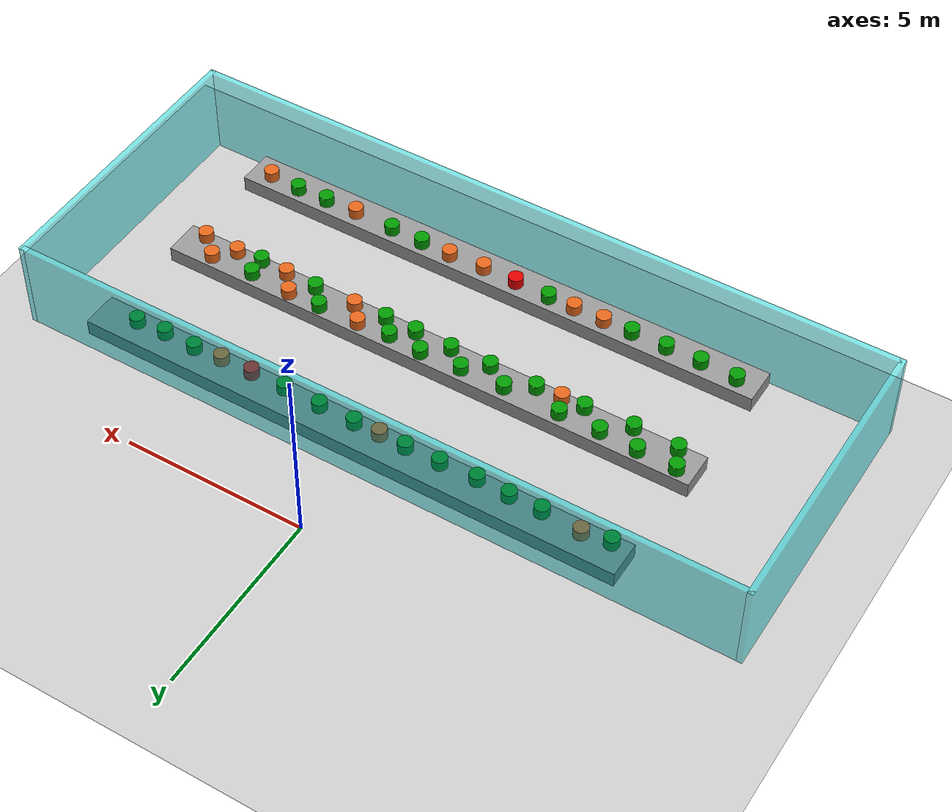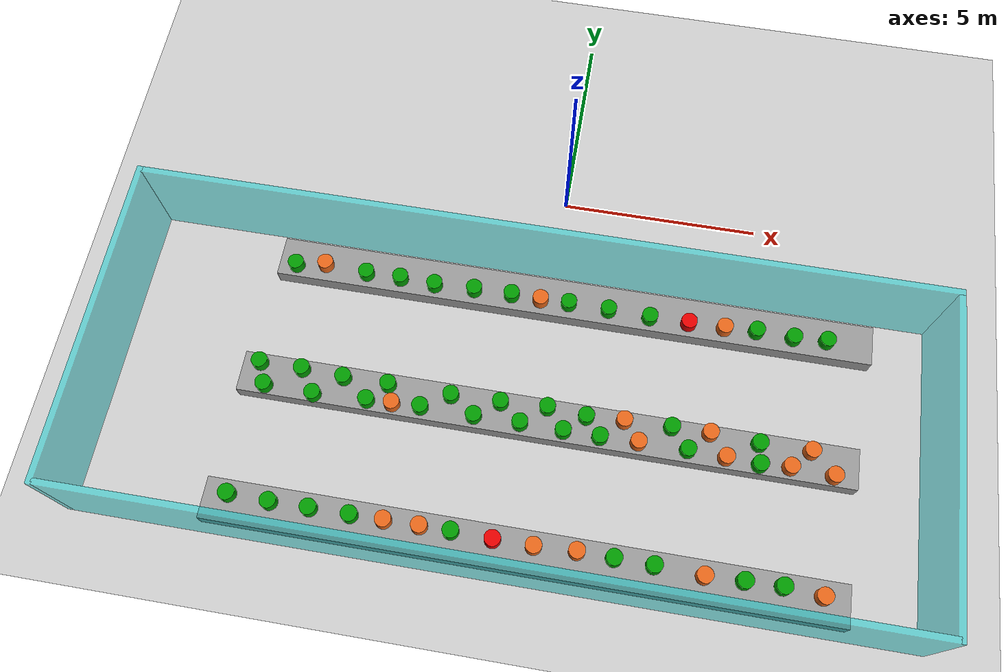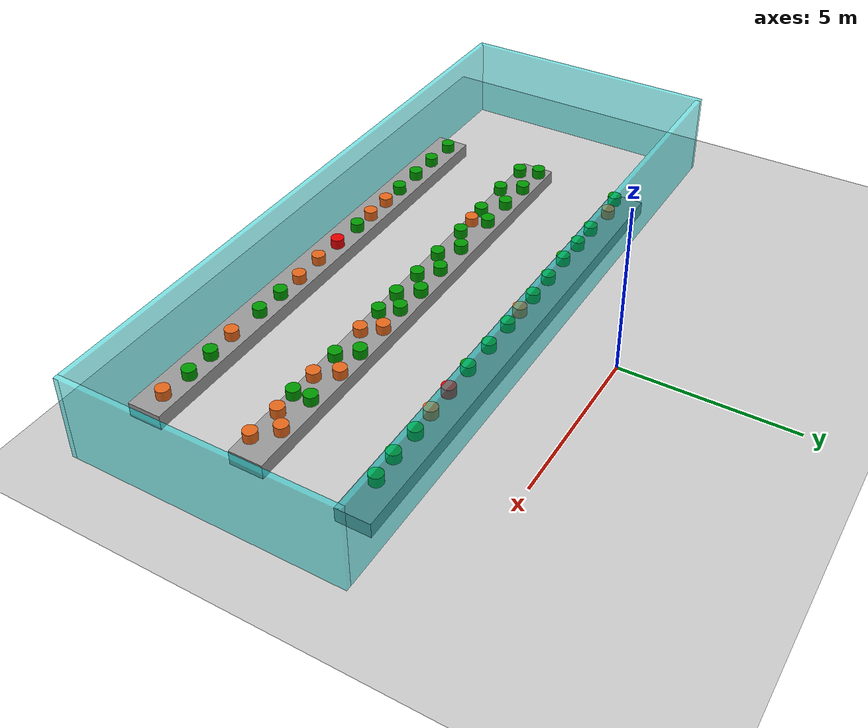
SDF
<sdf version="1.7">
 <world name="default">
  <light name="sun" type="directional">
   <pose>0 0 10 0 -0 0</pose>
   <diffuse>0.8 0.8 0.8 1</diffuse>
   <specular>0.2 0.2 0.2 1</specular>
   <attenuation>
    <range>1000</range>
    <constant>0.9</constant>
    <linear>0.01</linear>
    <quadratic>0.001</quadratic>
   </attenuation>
   <direction>-0.5 0.1 -0.9</direction>
   <spot><inner_angle>0</inner_angle><outer_angle>0</outer_angle><falloff>0</falloff></spot>
  </light>
  <model name="ground_plane">
   <static>1</static>
   <link name="link">
    <collision name="collision">
     <geometry><plane><normal>0 0 1</normal><size>100 100</size></plane></geometry>
     <surface>
      <contact><collide_bitmask>65535</collide_bitmask></contact>
      <friction><ode><mu>100</mu><mu2>50</mu2></ode></friction>
     </surface>
    </collision>
    <visual name="visual">
     <cast_shadows>0</cast_shadows>
     <geometry><plane><normal>0 0 1</normal><size>100 100</size></plane></geometry>
     <material>
      <script><uri>file://media/materials/scripts/gazebo.material</uri><name>Gazebo/Grey</name></script>
     </material>
    </visual>
   </link>
  </model>
  <gravity>0 0 -9.8</gravity>
  <magnetic_field>6e-06 2.3e-05 -4.2e-05</magnetic_field>
  <atmosphere type="adiabatic"/>
  <physics type="ode">
   <max_step_size>0.001</max_step_size>
   <real_time_factor>1</real_time_factor>
   <real_time_update_rate>1000</real_time_update_rate>
  </physics>
  <scene><ambient>0.4 0.4 0.4 1</ambient><background>0.7 0.7 0.7 1</background><shadows>1</shadows></scene>
  <spherical_coordinates>
   <surface_model>EARTH_WGS84</surface_model>
   <latitude_deg>0</latitude_deg>
   <longitude_deg>0</longitude_deg>
   <elevation>0</elevation>
   <heading_deg>0</heading_deg>
  </spherical_coordinates>
  <model name="Test_Bench">
   <link name="link_1">
    <inertial>
     <mass>6.47546</mass>
     <inertia><ixx>0.639529</ixx><ixy>0</ixy><ixz>0</ixz><iyy>122.309</iyy><iyz>0</iyz><izz>122.749</izz></inertia>
    </inertial>
    <pose>-0 4e-06 0 0 -0 0</pose>
    <visual name="visual">
     <geometry><box><size>15.049 1 0.430283</size></box></geometry>
     <material>
      <lighting>1</lighting>
      <script><uri>file://media/materials/scripts/gazebo.material</uri><name>Gazebo/Grey</name></script>
      <shader type="pixel"/>
     </material>
    </visual>
    <collision name="collision">
     <geometry><box><size>15.049 1 0.430283</size></box></geometry>
     <surface>
      <friction>
       <ode><mu>1</mu><mu2>1</mu2><fdir1>0 0 0</fdir1><slip1>0</slip1><slip2>0</slip2></ode>
       <torsional>
        <coefficient>1</coefficient>
        <patch_radius>0</patch_radius>
        <surface_radius>0</surface_radius>
        <use_patch_radius>1</use_patch_radius>
        <ode><slip>0</slip></ode>
       </torsional>
      </friction>
      <bounce><restitution_coefficient>0</restitution_coefficient><threshold>1e+06</threshold></bounce>
      <contact>
       <collide_without_contact>0</collide_without_contact>
       <collide_without_contact_bitmask>1</collide_without_contact_bitmask>
       <collide_bitmask>1</collide_bitmask>
       <ode>
        <soft_cfm>0</soft_cfm>
        <soft_erp>0.2</soft_erp>
        <kp>1e+13</kp>
        <kd>1</kd>
        <max_vel>0.01</max_vel>
        <min_depth>0</min_depth>
       </ode>
       <bullet>
        <split_impulse>1</split_impulse>
        <split_impulse_penetration_threshold>-0.01</split_impulse_penetration_threshold>
        <soft_cfm>0</soft_cfm>
        <soft_erp>0.2</soft_erp>
        <kp>1e+13</kp>
        <kd>1</kd>
       </bullet>
      </contact>
     </surface>
    </collision>
   </link>
   <static>0</static>
   <pose>0.548935 -2.85971 0.205889 -0.000489 3.2e-05 1.1e-05</pose>
  </model>
  <model name="Test_Bench_clone">
   <link name="link_1">
    <inertial>
     <mass>6.47546</mass>
     <inertia><ixx>0.639529</ixx><ixy>0</ixy><ixz>0</ixz><iyy>122.309</iyy><iyz>0</iyz><izz>122.749</izz></inertia>
    </inertial>
    <pose>-0 4e-06 0 0 -0 0</pose>
    <visual name="visual">
     <geometry><box><size>15.049 1 0.430283</size></box></geometry>
     <material>
      <lighting>1</lighting>
      <script><uri>file://media/materials/scripts/gazebo.material</uri><name>Gazebo/Grey</name></script>
      <shader type="pixel"/>
     </material>
    </visual>
    <collision name="collision">
     <geometry><box><size>15.049 1 0.430283</size></box></geometry>
     <surface>
      <friction>
       <ode><mu>1</mu><mu2>1</mu2><fdir1>0 0 0</fdir1><slip1>0</slip1><slip2>0</slip2></ode>
       <torsional>
        <coefficient>1</coefficient>
        <patch_radius>0</patch_radius>
        <surface_radius>0</surface_radius>
        <use_patch_radius>1</use_patch_radius>
        <ode><slip>0</slip></ode>
       </torsional>
      </friction>
      <bounce><restitution_coefficient>0</restitution_coefficient><threshold>1e+06</threshold></bounce>
      <contact>
       <collide_without_contact>0</collide_without_contact>
       <collide_without_contact_bitmask>1</collide_without_contact_bitmask>
       <collide_bitmask>1</collide_bitmask>
       <ode>
        <soft_cfm>0</soft_cfm>
        <soft_erp>0.2</soft_erp>
        <kp>1e+13</kp>
        <kd>1</kd>
        <max_vel>0.01</max_vel>
        <min_depth>0</min_depth>
       </ode>
       <bullet>
        <split_impulse>1</split_impulse>
        <split_impulse_penetration_threshold>-0.01</split_impulse_penetration_threshold>
        <soft_cfm>0</soft_cfm>
        <soft_erp>0.2</soft_erp>
        <kp>1e+13</kp>
        <kd>1</kd>
       </bullet>
      </contact>
     </surface>
    </collision>
   </link>
   <static>0</static>
   <pose>0.345725 -6.0582 0.210803 6.6e-05 -8e-06 2e-06</pose>
  </model>
  <model name="Test_Bench_clone_0">
   <link name="link_1">
    <inertial>
     <mass>6.47546</mass>
     <inertia><ixx>0.639529</ixx><ixy>0</ixy><ixz>0</ixz><iyy>122.309</iyy><iyz>0</iyz><izz>122.749</izz></inertia>
    </inertial>
    <pose>-0 4e-06 0 0 -0 0</pose>
    <visual name="visual">
     <geometry><box><size>15.049 1 0.430283</size></box></geometry>
     <material>
      <lighting>1</lighting>
      <script><uri>file://media/materials/scripts/gazebo.material</uri><name>Gazebo/Grey</name></script>
      <shader type="pixel"/>
     </material>
    </visual>
    <collision name="collision">
     <geometry><box><size>15.049 1 0.430283</size></box></geometry>
     <surface>
      <friction>
       <ode><mu>1</mu><mu2>1</mu2><fdir1>0 0 0</fdir1><slip1>0</slip1><slip2>0</slip2></ode>
       <torsional>
        <coefficient>1</coefficient>
        <patch_radius>0</patch_radius>
        <surface_radius>0</surface_radius>
        <use_patch_radius>1</use_patch_radius>
        <ode><slip>0</slip></ode>
       </torsional>
      </friction>
      <bounce><restitution_coefficient>0</restitution_coefficient><threshold>1e+06</threshold></bounce>
      <contact>
       <collide_without_contact>0</collide_without_contact>
       <collide_without_contact_bitmask>1</collide_without_contact_bitmask>
       <collide_bitmask>1</collide_bitmask>
       <ode>
        <soft_cfm>0</soft_cfm>
        <soft_erp>0.2</soft_erp>
        <kp>1e+13</kp>
        <kd>1</kd>
        <max_vel>0.01</max_vel>
        <min_depth>0</min_depth>
       </ode>
       <bullet>
        <split_impulse>1</split_impulse>
        <split_impulse_penetration_threshold>-0.01</split_impulse_penetration_threshold>
        <soft_cfm>0</soft_cfm>
        <soft_erp>0.2</soft_erp>
        <kp>1e+13</kp>
        <kd>1</kd>
       </bullet>
      </contact>
     </surface>
    </collision>
   </link>
   <static>0</static>
   <pose>0.286602 -9.2541 0.215141 0 -0 0</pose>
  </model>
  <model name="Test_Building2">
   <link name="Wall_3">
    <pose>0 2.93093 0 0 -0 0</pose>
    <inertial>
     <mass>1</mass>
     <inertia><ixx>1</ixx><ixy>0</ixy><ixz>0</ixz><iyy>1</iyy><iyz>0</iyz><izz>1</izz></inertia>
    </inertial>
    <visual name="Wall_3_Visual">
     <pose>0 0 1.25 0 -0 0</pose>
     <geometry><box><size>20 0.15 2.5</size></box></geometry>
     <material>
      <script><uri>file://media/materials/scripts/gazebo.material</uri><name>Gazebo/Grey</name></script>
      <ambient>0 0.808 0.816 1</ambient>
      <shader type="pixel"><normal_map>__default__</normal_map></shader>
      <diffuse>0.7 0.7 0.7 1</diffuse>
      <specular>0.01 0.01 0.01 1</specular>
      <emissive>0 0 0 1</emissive>
     </material>
     <meta><layer>0</layer></meta>
     <transparency>0.5</transparency>
    </visual>
    <collision name="Wall_3_Collision">
     <pose>0 0 1.25 0 -0 0</pose>
     <geometry><box><size>20 0.15 2.5</size></box></geometry>
     <surface>
      <friction>
       <ode><mu>1</mu><mu2>1</mu2><fdir1>0 0 0</fdir1><slip1>0</slip1><slip2>0</slip2></ode>
       <torsional>
        <coefficient>1</coefficient>
        <patch_radius>0</patch_radius>
        <surface_radius>0</surface_radius>
        <use_patch_radius>1</use_patch_radius>
        <ode><slip>0</slip></ode>
       </torsional>
      </friction>
      <bounce><restitution_coefficient>0</restitution_coefficient><threshold>1e+06</threshold></bounce>
      <contact>
       <collide_without_contact>0</collide_without_contact>
       <collide_without_contact_bitmask>1</collide_without_contact_bitmask>
       <collide_bitmask>1</collide_bitmask>
       <ode>
        <soft_cfm>0</soft_cfm>
        <soft_erp>0.2</soft_erp>
        <kp>1e+13</kp>
        <kd>1</kd>
        <max_vel>0.01</max_vel>
        <min_depth>0</min_depth>
       </ode>
       <bullet>
        <split_impulse>1</split_impulse>
        <split_impulse_penetration_threshold>-0.01</split_impulse_penetration_threshold>
        <soft_cfm>0</soft_cfm>
        <soft_erp>0.2</soft_erp>
        <kp>1e+13</kp>
        <kd>1</kd>
       </bullet>
      </contact>
     </surface>
    </collision>
   </link>
   <link name="Wall_4">
    <pose>9.925 -0.994068 0 0 0 -1.5708</pose>
    <inertial>
     <mass>1</mass>
     <inertia><ixx>1</ixx><ixy>0</ixy><ixz>0</ixz><iyy>1</iyy><iyz>0</iyz><izz>1</izz></inertia>
    </inertial>
    <visual name="Wall_4_Visual">
     <pose>0 0 1.25 0 -0 0</pose>
     <geometry><box><size>8 0.15 2.5</size></box></geometry>
     <material>
      <script><uri>file://media/materials/scripts/gazebo.material</uri><name>Gazebo/Grey</name></script>
      <ambient>0 0.808 0.816 1</ambient>
      <shader type="pixel"><normal_map>__default__</normal_map></shader>
      <diffuse>0.7 0.7 0.7 1</diffuse>
      <specular>0.01 0.01 0.01 1</specular>
      <emissive>0 0 0 1</emissive>
     </material>
     <meta><layer>0</layer></meta>
     <transparency>0.5</transparency>
    </visual>
    <collision name="Wall_4_Collision">
     <pose>0 0 1.25 0 -0 0</pose>
     <geometry><box><size>8 0.15 2.5</size></box></geometry>
     <surface>
      <friction>
       <ode><mu>1</mu><mu2>1</mu2><fdir1>0 0 0</fdir1><slip1>0</slip1><slip2>0</slip2></ode>
       <torsional>
        <coefficient>1</coefficient>
        <patch_radius>0</patch_radius>
        <surface_radius>0</surface_radius>
        <use_patch_radius>1</use_patch_radius>
        <ode><slip>0</slip></ode>
       </torsional>
      </friction>
      <bounce><restitution_coefficient>0</restitution_coefficient><threshold>1e+06</threshold></bounce>
      <contact>
       <collide_without_contact>0</collide_without_contact>
       <collide_without_contact_bitmask>1</collide_without_contact_bitmask>
       <collide_bitmask>1</collide_bitmask>
       <ode>
        <soft_cfm>0</soft_cfm>
        <soft_erp>0.2</soft_erp>
        <kp>1e+13</kp>
        <kd>1</kd>
        <max_vel>0.01</max_vel>
        <min_depth>0</min_depth>
       </ode>
       <bullet>
        <split_impulse>1</split_impulse>
        <split_impulse_penetration_threshold>-0.01</split_impulse_penetration_threshold>
        <soft_cfm>0</soft_cfm>
        <soft_erp>0.2</soft_erp>
        <kp>1e+13</kp>
        <kd>1</kd>
       </bullet>
      </contact>
     </surface>
    </collision>
   </link>
   <link name="Wall_5">
    <pose>0 -4.91907 0 0 -0 3.14159</pose>
    <inertial>
     <mass>1</mass>
     <inertia><ixx>1</ixx><ixy>0</ixy><ixz>0</ixz><iyy>1</iyy><iyz>0</iyz><izz>1</izz></inertia>
    </inertial>
    <visual name="Wall_5_Visual">
     <pose>0 0 1.25 0 -0 0</pose>
     <geometry><box><size>20 0.15 2.5</size></box></geometry>
     <material>
      <script><uri>file://media/materials/scripts/gazebo.material</uri><name>Gazebo/Grey</name></script>
      <ambient>0 0.808 0.816 1</ambient>
      <shader type="pixel"><normal_map>__default__</normal_map></shader>
      <diffuse>0.7 0.7 0.7 1</diffuse>
      <specular>0.01 0.01 0.01 1</specular>
      <emissive>0 0 0 1</emissive>
     </material>
     <meta><layer>0</layer></meta>
     <transparency>0.5</transparency>
    </visual>
    <collision name="Wall_5_Collision">
     <pose>0 0 1.25 0 -0 0</pose>
     <geometry><box><size>20 0.15 2.5</size></box></geometry>
     <surface>
      <friction>
       <ode><mu>1</mu><mu2>1</mu2><fdir1>0 0 0</fdir1><slip1>0</slip1><slip2>0</slip2></ode>
       <torsional>
        <coefficient>1</coefficient>
        <patch_radius>0</patch_radius>
        <surface_radius>0</surface_radius>
        <use_patch_radius>1</use_patch_radius>
        <ode><slip>0</slip></ode>
       </torsional>
      </friction>
      <bounce><restitution_coefficient>0</restitution_coefficient><threshold>1e+06</threshold></bounce>
      <contact>
       <collide_without_contact>0</collide_without_contact>
       <collide_without_contact_bitmask>1</collide_without_contact_bitmask>
       <collide_bitmask>1</collide_bitmask>
       <ode>
        <soft_cfm>0</soft_cfm>
        <soft_erp>0.2</soft_erp>
        <kp>1e+13</kp>
        <kd>1</kd>
        <max_vel>0.01</max_vel>
        <min_depth>0</min_depth>
       </ode>
       <bullet>
        <split_impulse>1</split_impulse>
        <split_impulse_penetration_threshold>-0.01</split_impulse_penetration_threshold>
        <soft_cfm>0</soft_cfm>
        <soft_erp>0.2</soft_erp>
        <kp>1e+13</kp>
        <kd>1</kd>
       </bullet>
      </contact>
     </surface>
    </collision>
   </link>
   <link name="Wall_6">
    <pose>-9.925 -0.994068 0 0 -0 1.5708</pose>
    <inertial>
     <mass>1</mass>
     <inertia><ixx>1</ixx><ixy>0</ixy><ixz>0</ixz><iyy>1</iyy><iyz>0</iyz><izz>1</izz></inertia>
    </inertial>
    <visual name="Wall_6_Visual">
     <pose>0 0 1.25 0 -0 0</pose>
     <geometry><box><size>8 0.15 2.5</size></box></geometry>
     <material>
      <script><uri>file://media/materials/scripts/gazebo.material</uri><name>Gazebo/Grey</name></script>
      <ambient>0 0.808 0.816 1</ambient>
      <shader type="pixel"><normal_map>__default__</normal_map></shader>
      <diffuse>0.7 0.7 0.7 1</diffuse>
      <specular>0.01 0.01 0.01 1</specular>
      <emissive>0 0 0 1</emissive>
     </material>
     <meta><layer>0</layer></meta>
     <transparency>0.5</transparency>
    </visual>
    <collision name="Wall_6_Collision">
     <pose>0 0 1.25 0 -0 0</pose>
     <geometry><box><size>8 0.15 2.5</size></box></geometry>
     <surface>
      <friction>
       <ode><mu>1</mu><mu2>1</mu2><fdir1>0 0 0</fdir1><slip1>0</slip1><slip2>0</slip2></ode>
       <torsional>
        <coefficient>1</coefficient>
        <patch_radius>0</patch_radius>
        <surface_radius>0</surface_radius>
        <use_patch_radius>1</use_patch_radius>
        <ode><slip>0</slip></ode>
       </torsional>
      </friction>
      <bounce><restitution_coefficient>0</restitution_coefficient><threshold>1e+06</threshold></bounce>
      <contact>
       <collide_without_contact>0</collide_without_contact>
       <collide_without_contact_bitmask>1</collide_without_contact_bitmask>
       <collide_bitmask>1</collide_bitmask>
       <ode>
        <soft_cfm>0</soft_cfm>
        <soft_erp>0.2</soft_erp>
        <kp>1e+13</kp>
        <kd>1</kd>
        <max_vel>0.01</max_vel>
        <min_depth>0</min_depth>
       </ode>
       <bullet>
        <split_impulse>1</split_impulse>
        <split_impulse_penetration_threshold>-0.01</split_impulse_penetration_threshold>
        <soft_cfm>0</soft_cfm>
        <soft_erp>0.2</soft_erp>
        <kp>1e+13</kp>
        <kd>1</kd>
       </bullet>
      </contact>
     </surface>
    </collision>
   </link>
   <static>1</static>
   <pose>-0.420117 -4.99407 0 0 -0 0</pose>
  </model>
  <model name="Test_pot_green">
   <link name="link_0">
    <inertial>
     <mass>0.044841</mass>
     <inertia>
      <ixx>0.00074807</ixx>
      <ixy>0</ixy>
      <ixz>0</ixz>
      <iyy>0.00074807</iyy>
      <iyz>0</iyz>
      <izz>0.00086495</izz>
     </inertia>
    </inertial>
    <pose>3e-06 1e-06 0 0 -0 0</pose>
    <visual name="visual">
     <geometry><cylinder><radius>0.196415</radius><length>0.290612</length></cylinder></geometry>
     <material>
      <lighting>1</lighting>
      <script><uri>file://media/materials/scripts/gazebo.material</uri><name>Gazebo/Grey</name></script>
      <shader type="pixel"><normal_map>__default__</normal_map></shader>
      <diffuse>0 0.6 0 0</diffuse>
      <ambient>0.3 0.3 0.3 1</ambient>
      <specular>0.01 0.01 0.01 1</specular>
      <emissive>0 0 0 1</emissive>
     </material>
    </visual>
    <collision name="collision">
     <geometry><cylinder><radius>0.196415</radius><length>0.290612</length></cylinder></geometry>
     <surface>
      <friction>
       <ode><mu>1</mu><mu2>1</mu2><fdir1>0 0 0</fdir1><slip1>0</slip1><slip2>0</slip2></ode>
       <torsional>
        <coefficient>1</coefficient>
        <patch_radius>0</patch_radius>
        <surface_radius>0</surface_radius>
        <use_patch_radius>1</use_patch_radius>
        <ode><slip>0</slip></ode>
       </torsional>
      </friction>
      <bounce><restitution_coefficient>0</restitution_coefficient><threshold>1e+06</threshold></bounce>
      <contact>
       <collide_without_contact>0</collide_without_contact>
       <collide_without_contact_bitmask>1</collide_without_contact_bitmask>
       <collide_bitmask>1</collide_bitmask>
       <ode>
        <soft_cfm>0</soft_cfm>
        <soft_erp>0.2</soft_erp>
        <kp>1e+13</kp>
        <kd>1</kd>
        <max_vel>0.01</max_vel>
        <min_depth>0</min_depth>
       </ode>
       <bullet>
        <split_impulse>1</split_impulse>
        <split_impulse_penetration_threshold>-0.01</split_impulse_penetration_threshold>
        <soft_cfm>0</soft_cfm>
        <soft_erp>0.2</soft_erp>
        <kp>1e+13</kp>
        <kd>1</kd>
       </bullet>
      </contact>
     </surface>
    </collision>
   </link>
   <static>0</static>
   <pose>-6.50437 -3.08139 0.575588 1e-06 6e-06 -0.000489</pose>
  </model>
  <model name="Test_pot_orange">
   <link name="link_0">
    <inertial>
     <mass>0.044841</mass>
     <inertia>
      <ixx>0.00074807</ixx>
      <ixy>0</ixy>
      <ixz>0</ixz>
      <iyy>0.00074807</iyy>
      <iyz>0</iyz>
      <izz>0.00086495</izz>
     </inertia>
    </inertial>
    <pose>3e-06 1e-06 -0 0 -0 0</pose>
    <visual name="visual">
     <geometry><cylinder><radius>0.196415</radius><length>0.290612</length></cylinder></geometry>
     <material>
      <lighting>1</lighting>
      <script><uri>file://media/materials/scripts/gazebo.material</uri><name>Gazebo/Grey</name></script>
      <shader type="pixel"><normal_map>__default__</normal_map></shader>
      <ambient>0.3 0.3 0.3 1</ambient>
      <diffuse>0.9 0.4 0.1 1</diffuse>
      <specular>0.01 0.01 0.01 1</specular>
      <emissive>0 0 0 1</emissive>
     </material>
    </visual>
    <collision name="collision">
     <geometry><cylinder><radius>0.196415</radius><length>0.290612</length></cylinder></geometry>
     <surface>
      <friction>
       <ode><mu>1</mu><mu2>1</mu2><fdir1>0 0 0</fdir1><slip1>0</slip1><slip2>0</slip2></ode>
       <torsional>
        <coefficient>1</coefficient>
        <patch_radius>0</patch_radius>
        <surface_radius>0</surface_radius>
        <use_patch_radius>1</use_patch_radius>
        <ode><slip>0</slip></ode>
       </torsional>
      </friction>
      <bounce><restitution_coefficient>0</restitution_coefficient><threshold>1e+06</threshold></bounce>
      <contact>
       <collide_without_contact>0</collide_without_contact>
       <collide_without_contact_bitmask>1</collide_without_contact_bitmask>
       <collide_bitmask>1</collide_bitmask>
       <ode>
        <soft_cfm>0</soft_cfm>
        <soft_erp>0.2</soft_erp>
        <kp>1e+13</kp>
        <kd>1</kd>
        <max_vel>0.01</max_vel>
        <min_depth>0</min_depth>
       </ode>
       <bullet>
        <split_impulse>1</split_impulse>
        <split_impulse_penetration_threshold>-0.01</split_impulse_penetration_threshold>
        <soft_cfm>0</soft_cfm>
        <soft_erp>0.2</soft_erp>
        <kp>1e+13</kp>
        <kd>1</kd>
       </bullet>
      </contact>
     </surface>
    </collision>
   </link>
   <static>0</static>
   <pose>-5.76716 -2.95767 0.575586 3.8e-05 1e-06 -0.000459</pose>
  </model>
  <model name="Test_pot_red">
   <link name="link_0">
    <inertial>
     <mass>0.044841</mass>
     <inertia>
      <ixx>0.00074807</ixx>
      <ixy>0</ixy>
      <ixz>0</ixz>
      <iyy>0.00074807</iyy>
      <iyz>0</iyz>
      <izz>0.00086495</izz>
     </inertia>
    </inertial>
    <pose>3e-06 1e-06 -0 0 -0 0</pose>
    <visual name="visual">
     <geometry><cylinder><radius>0.196415</radius><length>0.290612</length></cylinder></geometry>
     <material>
      <lighting>1</lighting>
      <script><uri>file://media/materials/scripts/gazebo.material</uri><name>Gazebo/Grey</name></script>
      <shader type="pixel"><normal_map>__default__</normal_map></shader>
      <ambient>0.3 0.3 0.3 1</ambient>
      <diffuse>0.9 0 0 1</diffuse>
      <specular>0.01 0.01 0.01 1</specular>
      <emissive>0 0 0 1</emissive>
     </material>
    </visual>
    <collision name="collision">
     <geometry><cylinder><radius>0.196415</radius><length>0.290612</length></cylinder></geometry>
     <surface>
      <friction>
       <ode><mu>1</mu><mu2>1</mu2><fdir1>0 0 0</fdir1><slip1>0</slip1><slip2>0</slip2></ode>
       <torsional>
        <coefficient>1</coefficient>
        <patch_radius>0</patch_radius>
        <surface_radius>0</surface_radius>
        <use_patch_radius>1</use_patch_radius>
        <ode><slip>0</slip></ode>
       </torsional>
      </friction>
      <bounce><restitution_coefficient>0</restitution_coefficient><threshold>1e+06</threshold></bounce>
      <contact>
       <collide_without_contact>0</collide_without_contact>
       <collide_without_contact_bitmask>1</collide_without_contact_bitmask>
       <collide_bitmask>1</collide_bitmask>
       <ode>
        <soft_cfm>0</soft_cfm>
        <soft_erp>0.2</soft_erp>
        <kp>1e+13</kp>
        <kd>1</kd>
        <max_vel>0.01</max_vel>
        <min_depth>0</min_depth>
       </ode>
       <bullet>
        <split_impulse>1</split_impulse>
        <split_impulse_penetration_threshold>-0.01</split_impulse_penetration_threshold>
        <soft_cfm>0</soft_cfm>
        <soft_erp>0.2</soft_erp>
        <kp>1e+13</kp>
        <kd>1</kd>
       </bullet>
      </contact>
     </surface>
    </collision>
   </link>
   <static>0</static>
   <pose>3.5117 -3.04366 0.575586 3.8e-05 1e-06 -0.000459</pose>
  </model>
  <model name="Test_pot_green_clone">
   <link name="link_0">
    <inertial>
     <mass>0.044841</mass>
     <inertia>
      <ixx>0.00074807</ixx>
      <ixy>0</ixy>
      <ixz>0</ixz>
      <iyy>0.00074807</iyy>
      <iyz>0</iyz>
      <izz>0.00086495</izz>
     </inertia>
    </inertial>
    <pose>3e-06 1e-06 0 0 -0 0</pose>
    <visual name="visual">
     <geometry><cylinder><radius>0.196415</radius><length>0.290612</length></cylinder></geometry>
     <material>
      <lighting>1</lighting>
      <script><uri>file://media/materials/scripts/gazebo.material</uri><name>Gazebo/Grey</name></script>
      <shader type="pixel"><normal_map>__default__</normal_map></shader>
      <diffuse>0 0.6 0 0</diffuse>
      <ambient>0.3 0.3 0.3 1</ambient>
      <specular>0.01 0.01 0.01 1</specular>
      <emissive>0 0 0 1</emissive>
     </material>
    </visual>
    <collision name="collision">
     <geometry><cylinder><radius>0.196415</radius><length>0.290612</length></cylinder></geometry>
     <surface>
      <friction>
       <ode><mu>1</mu><mu2>1</mu2><fdir1>0 0 0</fdir1><slip1>0</slip1><slip2>0</slip2></ode>
       <torsional>
        <coefficient>1</coefficient>
        <patch_radius>0</patch_radius>
        <surface_radius>0</surface_radius>
        <use_patch_radius>1</use_patch_radius>
        <ode><slip>0</slip></ode>
       </torsional>
      </friction>
      <bounce><restitution_coefficient>0</restitution_coefficient><threshold>1e+06</threshold></bounce>
      <contact>
       <collide_without_contact>0</collide_without_contact>
       <collide_without_contact_bitmask>1</collide_without_contact_bitmask>
       <collide_bitmask>1</collide_bitmask>
       <ode>
        <soft_cfm>0</soft_cfm>
        <soft_erp>0.2</soft_erp>
        <kp>1e+13</kp>
        <kd>1</kd>
        <max_vel>0.01</max_vel>
        <min_depth>0</min_depth>
       </ode>
       <bullet>
        <split_impulse>1</split_impulse>
        <split_impulse_penetration_threshold>-0.01</split_impulse_penetration_threshold>
        <soft_cfm>0</soft_cfm>
        <soft_erp>0.2</soft_erp>
        <kp>1e+13</kp>
        <kd>1</kd>
       </bullet>
      </contact>
     </surface>
    </collision>
   </link>
   <static>0</static>
   <pose>-4.69033 -3.02874 0.575588 1e-06 6e-06 -0.000489</pose>
  </model>
  <model name="Test_pot_green_clone_0">
   <link name="link_0">
    <inertial>
     <mass>0.044841</mass>
     <inertia>
      <ixx>0.00074807</ixx>
      <ixy>0</ixy>
      <ixz>0</ixz>
      <iyy>0.00074807</iyy>
      <iyz>0</iyz>
      <izz>0.00086495</izz>
     </inertia>
    </inertial>
    <pose>3e-06 1e-06 0 0 -0 0</pose>
    <visual name="visual">
     <geometry><cylinder><radius>0.196415</radius><length>0.290612</length></cylinder></geometry>
     <material>
      <lighting>1</lighting>
      <script><uri>file://media/materials/scripts/gazebo.material</uri><name>Gazebo/Grey</name></script>
      <shader type="pixel"><normal_map>__default__</normal_map></shader>
      <diffuse>0 0.6 0 0</diffuse>
      <ambient>0.3 0.3 0.3 1</ambient>
      <specular>0.01 0.01 0.01 1</specular>
      <emissive>0 0 0 1</emissive>
     </material>
    </visual>
    <collision name="collision">
     <geometry><cylinder><radius>0.196415</radius><length>0.290612</length></cylinder></geometry>
     <surface>
      <friction>
       <ode><mu>1</mu><mu2>1</mu2><fdir1>0 0 0</fdir1><slip1>0</slip1><slip2>0</slip2></ode>
       <torsional>
        <coefficient>1</coefficient>
        <patch_radius>0</patch_radius>
        <surface_radius>0</surface_radius>
        <use_patch_radius>1</use_patch_radius>
        <ode><slip>0</slip></ode>
       </torsional>
      </friction>
      <bounce><restitution_coefficient>0</restitution_coefficient><threshold>1e+06</threshold></bounce>
      <contact>
       <collide_without_contact>0</collide_without_contact>
       <collide_without_contact_bitmask>1</collide_without_contact_bitmask>
       <collide_bitmask>1</collide_bitmask>
       <ode>
        <soft_cfm>0</soft_cfm>
        <soft_erp>0.2</soft_erp>
        <kp>1e+13</kp>
        <kd>1</kd>
        <max_vel>0.01</max_vel>
        <min_depth>0</min_depth>
       </ode>
       <bullet>
        <split_impulse>1</split_impulse>
        <split_impulse_penetration_threshold>-0.01</split_impulse_penetration_threshold>
        <soft_cfm>0</soft_cfm>
        <soft_erp>0.2</soft_erp>
        <kp>1e+13</kp>
        <kd>1</kd>
       </bullet>
      </contact>
     </surface>
    </collision>
   </link>
   <static>0</static>
   <pose>-3.81267 -3.0248 0.575588 1e-06 6e-06 -0.000489</pose>
  </model>
  <model name="Test_pot_green_clone_1">
   <link name="link_0">
    <inertial>
     <mass>0.044841</mass>
     <inertia>
      <ixx>0.00074807</ixx>
      <ixy>0</ixy>
      <ixz>0</ixz>
      <iyy>0.00074807</iyy>
      <iyz>0</iyz>
      <izz>0.00086495</izz>
     </inertia>
    </inertial>
    <pose>3e-06 1e-06 0 0 -0 0</pose>
    <visual name="visual">
     <geometry><cylinder><radius>0.196415</radius><length>0.290612</length></cylinder></geometry>
     <material>
      <lighting>1</lighting>
      <script><uri>file://media/materials/scripts/gazebo.material</uri><name>Gazebo/Grey</name></script>
      <shader type="pixel"><normal_map>__default__</normal_map></shader>
      <diffuse>0 0.6 0 0</diffuse>
      <ambient>0.3 0.3 0.3 1</ambient>
      <specular>0.01 0.01 0.01 1</specular>
      <emissive>0 0 0 1</emissive>
     </material>
    </visual>
    <collision name="collision">
     <geometry><cylinder><radius>0.196415</radius><length>0.290612</length></cylinder></geometry>
     <surface>
      <friction>
       <ode><mu>1</mu><mu2>1</mu2><fdir1>0 0 0</fdir1><slip1>0</slip1><slip2>0</slip2></ode>
       <torsional>
        <coefficient>1</coefficient>
        <patch_radius>0</patch_radius>
        <surface_radius>0</surface_radius>
        <use_patch_radius>1</use_patch_radius>
        <ode><slip>0</slip></ode>
       </torsional>
      </friction>
      <bounce><restitution_coefficient>0</restitution_coefficient><threshold>1e+06</threshold></bounce>
      <contact>
       <collide_without_contact>0</collide_without_contact>
       <collide_without_contact_bitmask>1</collide_without_contact_bitmask>
       <collide_bitmask>1</collide_bitmask>
       <ode>
        <soft_cfm>0</soft_cfm>
        <soft_erp>0.2</soft_erp>
        <kp>1e+13</kp>
        <kd>1</kd>
        <max_vel>0.01</max_vel>
        <min_depth>0</min_depth>
       </ode>
       <bullet>
        <split_impulse>1</split_impulse>
        <split_impulse_penetration_threshold>-0.01</split_impulse_penetration_threshold>
        <soft_cfm>0</soft_cfm>
        <soft_erp>0.2</soft_erp>
        <kp>1e+13</kp>
        <kd>1</kd>
       </bullet>
      </contact>
     </surface>
    </collision>
   </link>
   <static>0</static>
   <pose>-2.92732 -3.05626 0.575588 1e-06 6e-06 -0.000489</pose>
  </model>
  <model name="Test_pot_green_clone_2">
   <link name="link_0">
    <inertial>
     <mass>0.044841</mass>
     <inertia>
      <ixx>0.00074807</ixx>
      <ixy>0</ixy>
      <ixz>0</ixz>
      <iyy>0.00074807</iyy>
      <iyz>0</iyz>
      <izz>0.00086495</izz>
     </inertia>
    </inertial>
    <pose>3e-06 1e-06 0 0 -0 0</pose>
    <visual name="visual">
     <geometry><cylinder><radius>0.196415</radius><length>0.290612</length></cylinder></geometry>
     <material>
      <lighting>1</lighting>
      <script><uri>file://media/materials/scripts/gazebo.material</uri><name>Gazebo/Grey</name></script>
      <shader type="pixel"><normal_map>__default__</normal_map></shader>
      <diffuse>0 0.6 0 0</diffuse>
      <ambient>0.3 0.3 0.3 1</ambient>
      <specular>0.01 0.01 0.01 1</specular>
      <emissive>0 0 0 1</emissive>
     </material>
    </visual>
    <collision name="collision">
     <geometry><cylinder><radius>0.196415</radius><length>0.290612</length></cylinder></geometry>
     <surface>
      <friction>
       <ode><mu>1</mu><mu2>1</mu2><fdir1>0 0 0</fdir1><slip1>0</slip1><slip2>0</slip2></ode>
       <torsional>
        <coefficient>1</coefficient>
        <patch_radius>0</patch_radius>
        <surface_radius>0</surface_radius>
        <use_patch_radius>1</use_patch_radius>
        <ode><slip>0</slip></ode>
       </torsional>
      </friction>
      <bounce><restitution_coefficient>0</restitution_coefficient><threshold>1e+06</threshold></bounce>
      <contact>
       <collide_without_contact>0</collide_without_contact>
       <collide_without_contact_bitmask>1</collide_without_contact_bitmask>
       <collide_bitmask>1</collide_bitmask>
       <ode>
        <soft_cfm>0</soft_cfm>
        <soft_erp>0.2</soft_erp>
        <kp>1e+13</kp>
        <kd>1</kd>
        <max_vel>0.01</max_vel>
        <min_depth>0</min_depth>
       </ode>
       <bullet>
        <split_impulse>1</split_impulse>
        <split_impulse_penetration_threshold>-0.01</split_impulse_penetration_threshold>
        <soft_cfm>0</soft_cfm>
        <soft_erp>0.2</soft_erp>
        <kp>1e+13</kp>
        <kd>1</kd>
       </bullet>
      </contact>
     </surface>
    </collision>
   </link>
   <static>0</static>
   <pose>-1.91725 -3.01875 0.575588 1e-06 6e-06 -0.000489</pose>
  </model>
  <model name="Test_pot_green_clone_3">
   <link name="link_0">
    <inertial>
     <mass>0.044841</mass>
     <inertia>
      <ixx>0.00074807</ixx>
      <ixy>0</ixy>
      <ixz>0</ixz>
      <iyy>0.00074807</iyy>
      <iyz>0</iyz>
      <izz>0.00086495</izz>
     </inertia>
    </inertial>
    <pose>3e-06 1e-06 0 0 -0 0</pose>
    <visual name="visual">
     <geometry><cylinder><radius>0.196415</radius><length>0.290612</length></cylinder></geometry>
     <material>
      <lighting>1</lighting>
      <script><uri>file://media/materials/scripts/gazebo.material</uri><name>Gazebo/Grey</name></script>
      <shader type="pixel"><normal_map>__default__</normal_map></shader>
      <diffuse>0 0.6 0 0</diffuse>
      <ambient>0.3 0.3 0.3 1</ambient>
      <specular>0.01 0.01 0.01 1</specular>
      <emissive>0 0 0 1</emissive>
     </material>
    </visual>
    <collision name="collision">
     <geometry><cylinder><radius>0.196415</radius><length>0.290612</length></cylinder></geometry>
     <surface>
      <friction>
       <ode><mu>1</mu><mu2>1</mu2><fdir1>0 0 0</fdir1><slip1>0</slip1><slip2>0</slip2></ode>
       <torsional>
        <coefficient>1</coefficient>
        <patch_radius>0</patch_radius>
        <surface_radius>0</surface_radius>
        <use_patch_radius>1</use_patch_radius>
        <ode><slip>0</slip></ode>
       </torsional>
      </friction>
      <bounce><restitution_coefficient>0</restitution_coefficient><threshold>1e+06</threshold></bounce>
      <contact>
       <collide_without_contact>0</collide_without_contact>
       <collide_without_contact_bitmask>1</collide_without_contact_bitmask>
       <collide_bitmask>1</collide_bitmask>
       <ode>
        <soft_cfm>0</soft_cfm>
        <soft_erp>0.2</soft_erp>
        <kp>1e+13</kp>
        <kd>1</kd>
        <max_vel>0.01</max_vel>
        <min_depth>0</min_depth>
       </ode>
       <bullet>
        <split_impulse>1</split_impulse>
        <split_impulse_penetration_threshold>-0.01</split_impulse_penetration_threshold>
        <soft_cfm>0</soft_cfm>
        <soft_erp>0.2</soft_erp>
        <kp>1e+13</kp>
        <kd>1</kd>
       </bullet>
      </contact>
     </surface>
    </collision>
   </link>
   <static>0</static>
   <pose>-0.965564 -3.00465 0.575588 1e-06 6e-06 -0.000489</pose>
  </model>
  <model name="Test_pot_green_clone_4">
   <link name="link_0">
    <inertial>
     <mass>0.044841</mass>
     <inertia>
      <ixx>0.00074807</ixx>
      <ixy>0</ixy>
      <ixz>0</ixz>
      <iyy>0.00074807</iyy>
      <iyz>0</iyz>
      <izz>0.00086495</izz>
     </inertia>
    </inertial>
    <pose>3e-06 1e-06 0 0 -0 0</pose>
    <visual name="visual">
     <geometry><cylinder><radius>0.196415</radius><length>0.290612</length></cylinder></geometry>
     <material>
      <lighting>1</lighting>
      <script><uri>file://media/materials/scripts/gazebo.material</uri><name>Gazebo/Grey</name></script>
      <shader type="pixel"><normal_map>__default__</normal_map></shader>
      <diffuse>0 0.6 0 0</diffuse>
      <ambient>0.3 0.3 0.3 1</ambient>
      <specular>0.01 0.01 0.01 1</specular>
      <emissive>0 0 0 1</emissive>
     </material>
    </visual>
    <collision name="collision">
     <geometry><cylinder><radius>0.196415</radius><length>0.290612</length></cylinder></geometry>
     <surface>
      <friction>
       <ode><mu>1</mu><mu2>1</mu2><fdir1>0 0 0</fdir1><slip1>0</slip1><slip2>0</slip2></ode>
       <torsional>
        <coefficient>1</coefficient>
        <patch_radius>0</patch_radius>
        <surface_radius>0</surface_radius>
        <use_patch_radius>1</use_patch_radius>
        <ode><slip>0</slip></ode>
       </torsional>
      </friction>
      <bounce><restitution_coefficient>0</restitution_coefficient><threshold>1e+06</threshold></bounce>
      <contact>
       <collide_without_contact>0</collide_without_contact>
       <collide_without_contact_bitmask>1</collide_without_contact_bitmask>
       <collide_bitmask>1</collide_bitmask>
       <ode>
        <soft_cfm>0</soft_cfm>
        <soft_erp>0.2</soft_erp>
        <kp>1e+13</kp>
        <kd>1</kd>
        <max_vel>0.01</max_vel>
        <min_depth>0</min_depth>
       </ode>
       <bullet>
        <split_impulse>1</split_impulse>
        <split_impulse_penetration_threshold>-0.01</split_impulse_penetration_threshold>
        <soft_cfm>0</soft_cfm>
        <soft_erp>0.2</soft_erp>
        <kp>1e+13</kp>
        <kd>1</kd>
       </bullet>
      </contact>
     </surface>
    </collision>
   </link>
   <static>0</static>
   <pose>-6.73376 -5.80677 0.575588 1e-06 6e-06 -0.000489</pose>
  </model>
  <model name="Test_pot_green_clone_5">
   <link name="link_0">
    <inertial>
     <mass>0.044841</mass>
     <inertia>
      <ixx>0.00074807</ixx>
      <ixy>0</ixy>
      <ixz>0</ixz>
      <iyy>0.00074807</iyy>
      <iyz>0</iyz>
      <izz>0.00086495</izz>
     </inertia>
    </inertial>
    <pose>3e-06 1e-06 0 0 -0 0</pose>
    <visual name="visual">
     <geometry><cylinder><radius>0.196415</radius><length>0.290612</length></cylinder></geometry>
     <material>
      <lighting>1</lighting>
      <script><uri>file://media/materials/scripts/gazebo.material</uri><name>Gazebo/Grey</name></script>
      <shader type="pixel"><normal_map>__default__</normal_map></shader>
      <diffuse>0 0.6 0 0</diffuse>
      <ambient>0.3 0.3 0.3 1</ambient>
      <specular>0.01 0.01 0.01 1</specular>
      <emissive>0 0 0 1</emissive>
     </material>
    </visual>
    <collision name="collision">
     <geometry><cylinder><radius>0.196415</radius><length>0.290612</length></cylinder></geometry>
     <surface>
      <friction>
       <ode><mu>1</mu><mu2>1</mu2><fdir1>0 0 0</fdir1><slip1>0</slip1><slip2>0</slip2></ode>
       <torsional>
        <coefficient>1</coefficient>
        <patch_radius>0</patch_radius>
        <surface_radius>0</surface_radius>
        <use_patch_radius>1</use_patch_radius>
        <ode><slip>0</slip></ode>
       </torsional>
      </friction>
      <bounce><restitution_coefficient>0</restitution_coefficient><threshold>1e+06</threshold></bounce>
      <contact>
       <collide_without_contact>0</collide_without_contact>
       <collide_without_contact_bitmask>1</collide_without_contact_bitmask>
       <collide_bitmask>1</collide_bitmask>
       <ode>
        <soft_cfm>0</soft_cfm>
        <soft_erp>0.2</soft_erp>
        <kp>1e+13</kp>
        <kd>1</kd>
        <max_vel>0.01</max_vel>
        <min_depth>0</min_depth>
       </ode>
       <bullet>
        <split_impulse>1</split_impulse>
        <split_impulse_penetration_threshold>-0.01</split_impulse_penetration_threshold>
        <soft_cfm>0</soft_cfm>
        <soft_erp>0.2</soft_erp>
        <kp>1e+13</kp>
        <kd>1</kd>
       </bullet>
      </contact>
     </surface>
    </collision>
   </link>
   <static>0</static>
   <pose>-5.67776 -5.81278 0.575588 1e-06 6e-06 -0.000489</pose>
  </model>
  <model name="Test_pot_green_clone_6">
   <link name="link_0">
    <inertial>
     <mass>0.044841</mass>
     <inertia>
      <ixx>0.00074807</ixx>
      <ixy>0</ixy>
      <ixz>0</ixz>
      <iyy>0.00074807</iyy>
      <iyz>0</iyz>
      <izz>0.00086495</izz>
     </inertia>
    </inertial>
    <pose>3e-06 1e-06 0 0 -0 0</pose>
    <visual name="visual">
     <geometry><cylinder><radius>0.196415</radius><length>0.290612</length></cylinder></geometry>
     <material>
      <lighting>1</lighting>
      <script><uri>file://media/materials/scripts/gazebo.material</uri><name>Gazebo/Grey</name></script>
      <shader type="pixel"><normal_map>__default__</normal_map></shader>
      <diffuse>0 0.6 0 0</diffuse>
      <ambient>0.3 0.3 0.3 1</ambient>
      <specular>0.01 0.01 0.01 1</specular>
      <emissive>0 0 0 1</emissive>
     </material>
    </visual>
    <collision name="collision">
     <geometry><cylinder><radius>0.196415</radius><length>0.290612</length></cylinder></geometry>
     <surface>
      <friction>
       <ode><mu>1</mu><mu2>1</mu2><fdir1>0 0 0</fdir1><slip1>0</slip1><slip2>0</slip2></ode>
       <torsional>
        <coefficient>1</coefficient>
        <patch_radius>0</patch_radius>
        <surface_radius>0</surface_radius>
        <use_patch_radius>1</use_patch_radius>
        <ode><slip>0</slip></ode>
       </torsional>
      </friction>
      <bounce><restitution_coefficient>0</restitution_coefficient><threshold>1e+06</threshold></bounce>
      <contact>
       <collide_without_contact>0</collide_without_contact>
       <collide_without_contact_bitmask>1</collide_without_contact_bitmask>
       <collide_bitmask>1</collide_bitmask>
       <ode>
        <soft_cfm>0</soft_cfm>
        <soft_erp>0.2</soft_erp>
        <kp>1e+13</kp>
        <kd>1</kd>
        <max_vel>0.01</max_vel>
        <min_depth>0</min_depth>
       </ode>
       <bullet>
        <split_impulse>1</split_impulse>
        <split_impulse_penetration_threshold>-0.01</split_impulse_penetration_threshold>
        <soft_cfm>0</soft_cfm>
        <soft_erp>0.2</soft_erp>
        <kp>1e+13</kp>
        <kd>1</kd>
       </bullet>
      </contact>
     </surface>
    </collision>
   </link>
   <static>0</static>
   <pose>-4.63391 -5.86067 0.575588 1e-06 6e-06 -0.000489</pose>
  </model>
  <model name="Test_pot_green_clone_7">
   <link name="link_0">
    <inertial>
     <mass>0.044841</mass>
     <inertia>
      <ixx>0.00074807</ixx>
      <ixy>0</ixy>
      <ixz>0</ixz>
      <iyy>0.00074807</iyy>
      <iyz>0</iyz>
      <izz>0.00086495</izz>
     </inertia>
    </inertial>
    <pose>3e-06 1e-06 0 0 -0 0</pose>
    <visual name="visual">
     <geometry><cylinder><radius>0.196415</radius><length>0.290612</length></cylinder></geometry>
     <material>
      <lighting>1</lighting>
      <script><uri>file://media/materials/scripts/gazebo.material</uri><name>Gazebo/Grey</name></script>
      <shader type="pixel"><normal_map>__default__</normal_map></shader>
      <diffuse>0 0.6 0 0</diffuse>
      <ambient>0.3 0.3 0.3 1</ambient>
      <specular>0.01 0.01 0.01 1</specular>
      <emissive>0 0 0 1</emissive>
     </material>
    </visual>
    <collision name="collision">
     <geometry><cylinder><radius>0.196415</radius><length>0.290612</length></cylinder></geometry>
     <surface>
      <friction>
       <ode><mu>1</mu><mu2>1</mu2><fdir1>0 0 0</fdir1><slip1>0</slip1><slip2>0</slip2></ode>
       <torsional>
        <coefficient>1</coefficient>
        <patch_radius>0</patch_radius>
        <surface_radius>0</surface_radius>
        <use_patch_radius>1</use_patch_radius>
        <ode><slip>0</slip></ode>
       </torsional>
      </friction>
      <bounce><restitution_coefficient>0</restitution_coefficient><threshold>1e+06</threshold></bounce>
      <contact>
       <collide_without_contact>0</collide_without_contact>
       <collide_without_contact_bitmask>1</collide_without_contact_bitmask>
       <collide_bitmask>1</collide_bitmask>
       <ode>
        <soft_cfm>0</soft_cfm>
        <soft_erp>0.2</soft_erp>
        <kp>1e+13</kp>
        <kd>1</kd>
        <max_vel>0.01</max_vel>
        <min_depth>0</min_depth>
       </ode>
       <bullet>
        <split_impulse>1</split_impulse>
        <split_impulse_penetration_threshold>-0.01</split_impulse_penetration_threshold>
        <soft_cfm>0</soft_cfm>
        <soft_erp>0.2</soft_erp>
        <kp>1e+13</kp>
        <kd>1</kd>
       </bullet>
      </contact>
     </surface>
    </collision>
   </link>
   <static>0</static>
   <pose>-6.49418 -6.35374 0.575588 1e-06 6e-06 -0.000489</pose>
  </model>
  <model name="Test_pot_green_clone_8">
   <link name="link_0">
    <inertial>
     <mass>0.044841</mass>
     <inertia>
      <ixx>0.00074807</ixx>
      <ixy>0</ixy>
      <ixz>0</ixz>
      <iyy>0.00074807</iyy>
      <iyz>0</iyz>
      <izz>0.00086495</izz>
     </inertia>
    </inertial>
    <pose>3e-06 1e-06 0 0 -0 0</pose>
    <visual name="visual">
     <geometry><cylinder><radius>0.196415</radius><length>0.290612</length></cylinder></geometry>
     <material>
      <lighting>1</lighting>
      <script><uri>file://media/materials/scripts/gazebo.material</uri><name>Gazebo/Grey</name></script>
      <shader type="pixel"><normal_map>__default__</normal_map></shader>
      <diffuse>0 0.6 0 0</diffuse>
      <ambient>0.3 0.3 0.3 1</ambient>
      <specular>0.01 0.01 0.01 1</specular>
      <emissive>0 0 0 1</emissive>
     </material>
    </visual>
    <collision name="collision">
     <geometry><cylinder><radius>0.196415</radius><length>0.290612</length></cylinder></geometry>
     <surface>
      <friction>
       <ode><mu>1</mu><mu2>1</mu2><fdir1>0 0 0</fdir1><slip1>0</slip1><slip2>0</slip2></ode>
       <torsional>
        <coefficient>1</coefficient>
        <patch_radius>0</patch_radius>
        <surface_radius>0</surface_radius>
        <use_patch_radius>1</use_patch_radius>
        <ode><slip>0</slip></ode>
       </torsional>
      </friction>
      <bounce><restitution_coefficient>0</restitution_coefficient><threshold>1e+06</threshold></bounce>
      <contact>
       <collide_without_contact>0</collide_without_contact>
       <collide_without_contact_bitmask>1</collide_without_contact_bitmask>
       <collide_bitmask>1</collide_bitmask>
       <ode>
        <soft_cfm>0</soft_cfm>
        <soft_erp>0.2</soft_erp>
        <kp>1e+13</kp>
        <kd>1</kd>
        <max_vel>0.01</max_vel>
        <min_depth>0</min_depth>
       </ode>
       <bullet>
        <split_impulse>1</split_impulse>
        <split_impulse_penetration_threshold>-0.01</split_impulse_penetration_threshold>
        <soft_cfm>0</soft_cfm>
        <soft_erp>0.2</soft_erp>
        <kp>1e+13</kp>
        <kd>1</kd>
       </bullet>
      </contact>
     </surface>
    </collision>
   </link>
   <static>0</static>
   <pose>-5.2738 -6.38669 0.575588 1e-06 6e-06 -0.000489</pose>
  </model>
  <model name="Test_pot_green_clone_9">
   <link name="link_0">
    <inertial>
     <mass>0.044841</mass>
     <inertia>
      <ixx>0.00074807</ixx>
      <ixy>0</ixy>
      <ixz>0</ixz>
      <iyy>0.00074807</iyy>
      <iyz>0</iyz>
      <izz>0.00086495</izz>
     </inertia>
    </inertial>
    <pose>3e-06 1e-06 0 0 -0 0</pose>
    <visual name="visual">
     <geometry><cylinder><radius>0.196415</radius><length>0.290612</length></cylinder></geometry>
     <material>
      <lighting>1</lighting>
      <script><uri>file://media/materials/scripts/gazebo.material</uri><name>Gazebo/Grey</name></script>
      <shader type="pixel"><normal_map>__default__</normal_map></shader>
      <diffuse>0 0.6 0 0</diffuse>
      <ambient>0.3 0.3 0.3 1</ambient>
      <specular>0.01 0.01 0.01 1</specular>
      <emissive>0 0 0 1</emissive>
     </material>
    </visual>
    <collision name="collision">
     <geometry><cylinder><radius>0.196415</radius><length>0.290612</length></cylinder></geometry>
     <surface>
      <friction>
       <ode><mu>1</mu><mu2>1</mu2><fdir1>0 0 0</fdir1><slip1>0</slip1><slip2>0</slip2></ode>
       <torsional>
        <coefficient>1</coefficient>
        <patch_radius>0</patch_radius>
        <surface_radius>0</surface_radius>
        <use_patch_radius>1</use_patch_radius>
        <ode><slip>0</slip></ode>
       </torsional>
      </friction>
      <bounce><restitution_coefficient>0</restitution_coefficient><threshold>1e+06</threshold></bounce>
      <contact>
       <collide_without_contact>0</collide_without_contact>
       <collide_without_contact_bitmask>1</collide_without_contact_bitmask>
       <collide_bitmask>1</collide_bitmask>
       <ode>
        <soft_cfm>0</soft_cfm>
        <soft_erp>0.2</soft_erp>
        <kp>1e+13</kp>
        <kd>1</kd>
        <max_vel>0.01</max_vel>
        <min_depth>0</min_depth>
       </ode>
       <bullet>
        <split_impulse>1</split_impulse>
        <split_impulse_penetration_threshold>-0.01</split_impulse_penetration_threshold>
        <soft_cfm>0</soft_cfm>
        <soft_erp>0.2</soft_erp>
        <kp>1e+13</kp>
        <kd>1</kd>
       </bullet>
      </contact>
     </surface>
    </collision>
   </link>
   <static>0</static>
   <pose>-3.95991 -6.3273 0.575588 1e-06 6e-06 -0.000489</pose>
  </model>
  <model name="Test_pot_green_clone_10">
   <link name="link_0">
    <inertial>
     <mass>0.044841</mass>
     <inertia>
      <ixx>0.00074807</ixx>
      <ixy>0</ixy>
      <ixz>0</ixz>
      <iyy>0.00074807</iyy>
      <iyz>0</iyz>
      <izz>0.00086495</izz>
     </inertia>
    </inertial>
    <pose>3e-06 1e-06 0 0 -0 0</pose>
    <visual name="visual">
     <geometry><cylinder><radius>0.196415</radius><length>0.290612</length></cylinder></geometry>
     <material>
      <lighting>1</lighting>
      <script><uri>file://media/materials/scripts/gazebo.material</uri><name>Gazebo/Grey</name></script>
      <shader type="pixel"><normal_map>__default__</normal_map></shader>
      <diffuse>0 0.6 0 0</diffuse>
      <ambient>0.3 0.3 0.3 1</ambient>
      <specular>0.01 0.01 0.01 1</specular>
      <emissive>0 0 0 1</emissive>
     </material>
    </visual>
    <collision name="collision">
     <geometry><cylinder><radius>0.196415</radius><length>0.290612</length></cylinder></geometry>
     <surface>
      <friction>
       <ode><mu>1</mu><mu2>1</mu2><fdir1>0 0 0</fdir1><slip1>0</slip1><slip2>0</slip2></ode>
       <torsional>
        <coefficient>1</coefficient>
        <patch_radius>0</patch_radius>
        <surface_radius>0</surface_radius>
        <use_patch_radius>1</use_patch_radius>
        <ode><slip>0</slip></ode>
       </torsional>
      </friction>
      <bounce><restitution_coefficient>0</restitution_coefficient><threshold>1e+06</threshold></bounce>
      <contact>
       <collide_without_contact>0</collide_without_contact>
       <collide_without_contact_bitmask>1</collide_without_contact_bitmask>
       <collide_bitmask>1</collide_bitmask>
       <ode>
        <soft_cfm>0</soft_cfm>
        <soft_erp>0.2</soft_erp>
        <kp>1e+13</kp>
        <kd>1</kd>
        <max_vel>0.01</max_vel>
        <min_depth>0</min_depth>
       </ode>
       <bullet>
        <split_impulse>1</split_impulse>
        <split_impulse_penetration_threshold>-0.01</split_impulse_penetration_threshold>
        <soft_cfm>0</soft_cfm>
        <soft_erp>0.2</soft_erp>
        <kp>1e+13</kp>
        <kd>1</kd>
       </bullet>
      </contact>
     </surface>
    </collision>
   </link>
   <static>0</static>
   <pose>-3.5193 -5.85781 0.575588 1e-06 6e-06 -0.000489</pose>
  </model>
  <model name="Test_pot_green_clone_11">
   <link name="link_0">
    <inertial>
     <mass>0.044841</mass>
     <inertia>
      <ixx>0.00074807</ixx>
      <ixy>0</ixy>
      <ixz>0</ixz>
      <iyy>0.00074807</iyy>
      <iyz>0</iyz>
      <izz>0.00086495</izz>
     </inertia>
    </inertial>
    <pose>3e-06 1e-06 0 0 -0 0</pose>
    <visual name="visual">
     <geometry><cylinder><radius>0.196415</radius><length>0.290612</length></cylinder></geometry>
     <material>
      <lighting>1</lighting>
      <script><uri>file://media/materials/scripts/gazebo.material</uri><name>Gazebo/Grey</name></script>
      <shader type="pixel"><normal_map>__default__</normal_map></shader>
      <diffuse>0 0.6 0 0</diffuse>
      <ambient>0.3 0.3 0.3 1</ambient>
      <specular>0.01 0.01 0.01 1</specular>
      <emissive>0 0 0 1</emissive>
     </material>
    </visual>
    <collision name="collision">
     <geometry><cylinder><radius>0.196415</radius><length>0.290612</length></cylinder></geometry>
     <surface>
      <friction>
       <ode><mu>1</mu><mu2>1</mu2><fdir1>0 0 0</fdir1><slip1>0</slip1><slip2>0</slip2></ode>
       <torsional>
        <coefficient>1</coefficient>
        <patch_radius>0</patch_radius>
        <surface_radius>0</surface_radius>
        <use_patch_radius>1</use_patch_radius>
        <ode><slip>0</slip></ode>
       </torsional>
      </friction>
      <bounce><restitution_coefficient>0</restitution_coefficient><threshold>1e+06</threshold></bounce>
      <contact>
       <collide_without_contact>0</collide_without_contact>
       <collide_without_contact_bitmask>1</collide_without_contact_bitmask>
       <collide_bitmask>1</collide_bitmask>
       <ode>
        <soft_cfm>0</soft_cfm>
        <soft_erp>0.2</soft_erp>
        <kp>1e+13</kp>
        <kd>1</kd>
        <max_vel>0.01</max_vel>
        <min_depth>0</min_depth>
       </ode>
       <bullet>
        <split_impulse>1</split_impulse>
        <split_impulse_penetration_threshold>-0.01</split_impulse_penetration_threshold>
        <soft_cfm>0</soft_cfm>
        <soft_erp>0.2</soft_erp>
        <kp>1e+13</kp>
        <kd>1</kd>
       </bullet>
      </contact>
     </surface>
    </collision>
   </link>
   <static>0</static>
   <pose>-2.64373 -6.28124 0.575588 1e-06 6e-06 -0.000489</pose>
  </model>
  <model name="Test_pot_green_clone_12">
   <link name="link_0">
    <inertial>
     <mass>0.044841</mass>
     <inertia>
      <ixx>0.00074807</ixx>
      <ixy>0</ixy>
      <ixz>0</ixz>
      <iyy>0.00074807</iyy>
      <iyz>0</iyz>
      <izz>0.00086495</izz>
     </inertia>
    </inertial>
    <pose>3e-06 1e-06 0 0 -0 0</pose>
    <visual name="visual">
     <geometry><cylinder><radius>0.196415</radius><length>0.290612</length></cylinder></geometry>
     <material>
      <lighting>1</lighting>
      <script><uri>file://media/materials/scripts/gazebo.material</uri><name>Gazebo/Grey</name></script>
      <shader type="pixel"><normal_map>__default__</normal_map></shader>
      <diffuse>0 0.6 0 0</diffuse>
      <ambient>0.3 0.3 0.3 1</ambient>
      <specular>0.01 0.01 0.01 1</specular>
      <emissive>0 0 0 1</emissive>
     </material>
    </visual>
    <collision name="collision">
     <geometry><cylinder><radius>0.196415</radius><length>0.290612</length></cylinder></geometry>
     <surface>
      <friction>
       <ode><mu>1</mu><mu2>1</mu2><fdir1>0 0 0</fdir1><slip1>0</slip1><slip2>0</slip2></ode>
       <torsional>
        <coefficient>1</coefficient>
        <patch_radius>0</patch_radius>
        <surface_radius>0</surface_radius>
        <use_patch_radius>1</use_patch_radius>
        <ode><slip>0</slip></ode>
       </torsional>
      </friction>
      <bounce><restitution_coefficient>0</restitution_coefficient><threshold>1e+06</threshold></bounce>
      <contact>
       <collide_without_contact>0</collide_without_contact>
       <collide_without_contact_bitmask>1</collide_without_contact_bitmask>
       <collide_bitmask>1</collide_bitmask>
       <ode>
        <soft_cfm>0</soft_cfm>
        <soft_erp>0.2</soft_erp>
        <kp>1e+13</kp>
        <kd>1</kd>
        <max_vel>0.01</max_vel>
        <min_depth>0</min_depth>
       </ode>
       <bullet>
        <split_impulse>1</split_impulse>
        <split_impulse_penetration_threshold>-0.01</split_impulse_penetration_threshold>
        <soft_cfm>0</soft_cfm>
        <soft_erp>0.2</soft_erp>
        <kp>1e+13</kp>
        <kd>1</kd>
       </bullet>
      </contact>
     </surface>
    </collision>
   </link>
   <static>0</static>
   <pose>-1.33861 -6.28993 0.575588 1e-06 6e-06 -0.000489</pose>
  </model>
  <model name="Test_pot_green_clone_13">
   <link name="link_0">
    <inertial>
     <mass>0.044841</mass>
     <inertia>
      <ixx>0.00074807</ixx>
      <ixy>0</ixy>
      <ixz>0</ixz>
      <iyy>0.00074807</iyy>
      <iyz>0</iyz>
      <izz>0.00086495</izz>
     </inertia>
    </inertial>
    <pose>3e-06 1e-06 0 0 -0 0</pose>
    <visual name="visual">
     <geometry><cylinder><radius>0.196415</radius><length>0.290612</length></cylinder></geometry>
     <material>
      <lighting>1</lighting>
      <script><uri>file://media/materials/scripts/gazebo.material</uri><name>Gazebo/Grey</name></script>
      <shader type="pixel"><normal_map>__default__</normal_map></shader>
      <diffuse>0 0.6 0 0</diffuse>
      <ambient>0.3 0.3 0.3 1</ambient>
      <specular>0.01 0.01 0.01 1</specular>
      <emissive>0 0 0 1</emissive>
     </material>
    </visual>
    <collision name="collision">
     <geometry><cylinder><radius>0.196415</radius><length>0.290612</length></cylinder></geometry>
     <surface>
      <friction>
       <ode><mu>1</mu><mu2>1</mu2><fdir1>0 0 0</fdir1><slip1>0</slip1><slip2>0</slip2></ode>
       <torsional>
        <coefficient>1</coefficient>
        <patch_radius>0</patch_radius>
        <surface_radius>0</surface_radius>
        <use_patch_radius>1</use_patch_radius>
        <ode><slip>0</slip></ode>
       </torsional>
      </friction>
      <bounce><restitution_coefficient>0</restitution_coefficient><threshold>1e+06</threshold></bounce>
      <contact>
       <collide_without_contact>0</collide_without_contact>
       <collide_without_contact_bitmask>1</collide_without_contact_bitmask>
       <collide_bitmask>1</collide_bitmask>
       <ode>
        <soft_cfm>0</soft_cfm>
        <soft_erp>0.2</soft_erp>
        <kp>1e+13</kp>
        <kd>1</kd>
        <max_vel>0.01</max_vel>
        <min_depth>0</min_depth>
       </ode>
       <bullet>
        <split_impulse>1</split_impulse>
        <split_impulse_penetration_threshold>-0.01</split_impulse_penetration_threshold>
        <soft_cfm>0</soft_cfm>
        <soft_erp>0.2</soft_erp>
        <kp>1e+13</kp>
        <kd>1</kd>
       </bullet>
      </contact>
     </surface>
    </collision>
   </link>
   <static>0</static>
   <pose>-1.96632 -5.87735 0.575588 1e-06 6e-06 -0.000489</pose>
  </model>
  <model name="Test_pot_green_clone_14">
   <link name="link_0">
    <inertial>
     <mass>0.044841</mass>
     <inertia>
      <ixx>0.00074807</ixx>
      <ixy>0</ixy>
      <ixz>0</ixz>
      <iyy>0.00074807</iyy>
      <iyz>0</iyz>
      <izz>0.00086495</izz>
     </inertia>
    </inertial>
    <pose>3e-06 1e-06 0 0 -0 0</pose>
    <visual name="visual">
     <geometry><cylinder><radius>0.196415</radius><length>0.290612</length></cylinder></geometry>
     <material>
      <lighting>1</lighting>
      <script><uri>file://media/materials/scripts/gazebo.material</uri><name>Gazebo/Grey</name></script>
      <shader type="pixel"><normal_map>__default__</normal_map></shader>
      <diffuse>0 0.6 0 0</diffuse>
      <ambient>0.3 0.3 0.3 1</ambient>
      <specular>0.01 0.01 0.01 1</specular>
      <emissive>0 0 0 1</emissive>
     </material>
    </visual>
    <collision name="collision">
     <geometry><cylinder><radius>0.196415</radius><length>0.290612</length></cylinder></geometry>
     <surface>
      <friction>
       <ode><mu>1</mu><mu2>1</mu2><fdir1>0 0 0</fdir1><slip1>0</slip1><slip2>0</slip2></ode>
       <torsional>
        <coefficient>1</coefficient>
        <patch_radius>0</patch_radius>
        <surface_radius>0</surface_radius>
        <use_patch_radius>1</use_patch_radius>
        <ode><slip>0</slip></ode>
       </torsional>
      </friction>
      <bounce><restitution_coefficient>0</restitution_coefficient><threshold>1e+06</threshold></bounce>
      <contact>
       <collide_without_contact>0</collide_without_contact>
       <collide_without_contact_bitmask>1</collide_without_contact_bitmask>
       <collide_bitmask>1</collide_bitmask>
       <ode>
        <soft_cfm>0</soft_cfm>
        <soft_erp>0.2</soft_erp>
        <kp>1e+13</kp>
        <kd>1</kd>
        <max_vel>0.01</max_vel>
        <min_depth>0</min_depth>
       </ode>
       <bullet>
        <split_impulse>1</split_impulse>
        <split_impulse_penetration_threshold>-0.01</split_impulse_penetration_threshold>
        <soft_cfm>0</soft_cfm>
        <soft_erp>0.2</soft_erp>
        <kp>1e+13</kp>
        <kd>1</kd>
       </bullet>
      </contact>
     </surface>
    </collision>
   </link>
   <static>0</static>
   <pose>-0.210467 -6.28115 0.575588 1e-06 6e-06 -0.000489</pose>
  </model>
  <model name="Test_pot_green_clone_15">
   <link name="link_0">
    <inertial>
     <mass>0.044841</mass>
     <inertia>
      <ixx>0.00074807</ixx>
      <ixy>0</ixy>
      <ixz>0</ixz>
      <iyy>0.00074807</iyy>
      <iyz>0</iyz>
      <izz>0.00086495</izz>
     </inertia>
    </inertial>
    <pose>3e-06 1e-06 0 0 -0 0</pose>
    <visual name="visual">
     <geometry><cylinder><radius>0.196415</radius><length>0.290612</length></cylinder></geometry>
     <material>
      <lighting>1</lighting>
      <script><uri>file://media/materials/scripts/gazebo.material</uri><name>Gazebo/Grey</name></script>
      <shader type="pixel"><normal_map>__default__</normal_map></shader>
      <diffuse>0 0.6 0 0</diffuse>
      <ambient>0.3 0.3 0.3 1</ambient>
      <specular>0.01 0.01 0.01 1</specular>
      <emissive>0 0 0 1</emissive>
     </material>
    </visual>
    <collision name="collision">
     <geometry><cylinder><radius>0.196415</radius><length>0.290612</length></cylinder></geometry>
     <surface>
      <friction>
       <ode><mu>1</mu><mu2>1</mu2><fdir1>0 0 0</fdir1><slip1>0</slip1><slip2>0</slip2></ode>
       <torsional>
        <coefficient>1</coefficient>
        <patch_radius>0</patch_radius>
        <surface_radius>0</surface_radius>
        <use_patch_radius>1</use_patch_radius>
        <ode><slip>0</slip></ode>
       </torsional>
      </friction>
      <bounce><restitution_coefficient>0</restitution_coefficient><threshold>1e+06</threshold></bounce>
      <contact>
       <collide_without_contact>0</collide_without_contact>
       <collide_without_contact_bitmask>1</collide_without_contact_bitmask>
       <collide_bitmask>1</collide_bitmask>
       <ode>
        <soft_cfm>0</soft_cfm>
        <soft_erp>0.2</soft_erp>
        <kp>1e+13</kp>
        <kd>1</kd>
        <max_vel>0.01</max_vel>
        <min_depth>0</min_depth>
       </ode>
       <bullet>
        <split_impulse>1</split_impulse>
        <split_impulse_penetration_threshold>-0.01</split_impulse_penetration_threshold>
        <soft_cfm>0</soft_cfm>
        <soft_erp>0.2</soft_erp>
        <kp>1e+13</kp>
        <kd>1</kd>
       </bullet>
      </contact>
     </surface>
    </collision>
   </link>
   <static>0</static>
   <pose>-0.752794 -5.8525 0.575588 1e-06 6e-06 -0.000489</pose>
  </model>
  <model name="Test_pot_green_clone_16">
   <link name="link_0">
    <inertial>
     <mass>0.044841</mass>
     <inertia>
      <ixx>0.00074807</ixx>
      <ixy>0</ixy>
      <ixz>0</ixz>
      <iyy>0.00074807</iyy>
      <iyz>0</iyz>
      <izz>0.00086495</izz>
     </inertia>
    </inertial>
    <pose>3e-06 1e-06 0 0 -0 0</pose>
    <visual name="visual">
     <geometry><cylinder><radius>0.196415</radius><length>0.290612</length></cylinder></geometry>
     <material>
      <lighting>1</lighting>
      <script><uri>file://media/materials/scripts/gazebo.material</uri><name>Gazebo/Grey</name></script>
      <shader type="pixel"><normal_map>__default__</normal_map></shader>
      <diffuse>0 0.6 0 0</diffuse>
      <ambient>0.3 0.3 0.3 1</ambient>
      <specular>0.01 0.01 0.01 1</specular>
      <emissive>0 0 0 1</emissive>
     </material>
    </visual>
    <collision name="collision">
     <geometry><cylinder><radius>0.196415</radius><length>0.290612</length></cylinder></geometry>
     <surface>
      <friction>
       <ode><mu>1</mu><mu2>1</mu2><fdir1>0 0 0</fdir1><slip1>0</slip1><slip2>0</slip2></ode>
       <torsional>
        <coefficient>1</coefficient>
        <patch_radius>0</patch_radius>
        <surface_radius>0</surface_radius>
        <use_patch_radius>1</use_patch_radius>
        <ode><slip>0</slip></ode>
       </torsional>
      </friction>
      <bounce><restitution_coefficient>0</restitution_coefficient><threshold>1e+06</threshold></bounce>
      <contact>
       <collide_without_contact>0</collide_without_contact>
       <collide_without_contact_bitmask>1</collide_without_contact_bitmask>
       <collide_bitmask>1</collide_bitmask>
       <ode>
        <soft_cfm>0</soft_cfm>
        <soft_erp>0.2</soft_erp>
        <kp>1e+13</kp>
        <kd>1</kd>
        <max_vel>0.01</max_vel>
        <min_depth>0</min_depth>
       </ode>
       <bullet>
        <split_impulse>1</split_impulse>
        <split_impulse_penetration_threshold>-0.01</split_impulse_penetration_threshold>
        <soft_cfm>0</soft_cfm>
        <soft_erp>0.2</soft_erp>
        <kp>1e+13</kp>
        <kd>1</kd>
       </bullet>
      </contact>
     </surface>
    </collision>
   </link>
   <static>0</static>
   <pose>0.837026 -6.30449 0.575588 1e-06 6e-06 -0.000489</pose>
  </model>
  <model name="Test_pot_green_clone_17">
   <link name="link_0">
    <inertial>
     <mass>0.044841</mass>
     <inertia>
      <ixx>0.00074807</ixx>
      <ixy>0</ixy>
      <ixz>0</ixz>
      <iyy>0.00074807</iyy>
      <iyz>0</iyz>
      <izz>0.00086495</izz>
     </inertia>
    </inertial>
    <pose>3e-06 1e-06 0 0 -0 0</pose>
    <visual name="visual">
     <geometry><cylinder><radius>0.196415</radius><length>0.290612</length></cylinder></geometry>
     <material>
      <lighting>1</lighting>
      <script><uri>file://media/materials/scripts/gazebo.material</uri><name>Gazebo/Grey</name></script>
      <shader type="pixel"><normal_map>__default__</normal_map></shader>
      <diffuse>0 0.6 0 0</diffuse>
      <ambient>0.3 0.3 0.3 1</ambient>
      <specular>0.01 0.01 0.01 1</specular>
      <emissive>0 0 0 1</emissive>
     </material>
    </visual>
    <collision name="collision">
     <geometry><cylinder><radius>0.196415</radius><length>0.290612</length></cylinder></geometry>
     <surface>
      <friction>
       <ode><mu>1</mu><mu2>1</mu2><fdir1>0 0 0</fdir1><slip1>0</slip1><slip2>0</slip2></ode>
       <torsional>
        <coefficient>1</coefficient>
        <patch_radius>0</patch_radius>
        <surface_radius>0</surface_radius>
        <use_patch_radius>1</use_patch_radius>
        <ode><slip>0</slip></ode>
       </torsional>
      </friction>
      <bounce><restitution_coefficient>0</restitution_coefficient><threshold>1e+06</threshold></bounce>
      <contact>
       <collide_without_contact>0</collide_without_contact>
       <collide_without_contact_bitmask>1</collide_without_contact_bitmask>
       <collide_bitmask>1</collide_bitmask>
       <ode>
        <soft_cfm>0</soft_cfm>
        <soft_erp>0.2</soft_erp>
        <kp>1e+13</kp>
        <kd>1</kd>
        <max_vel>0.01</max_vel>
        <min_depth>0</min_depth>
       </ode>
       <bullet>
        <split_impulse>1</split_impulse>
        <split_impulse_penetration_threshold>-0.01</split_impulse_penetration_threshold>
        <soft_cfm>0</soft_cfm>
        <soft_erp>0.2</soft_erp>
        <kp>1e+13</kp>
        <kd>1</kd>
       </bullet>
      </contact>
     </surface>
    </collision>
   </link>
   <static>0</static>
   <pose>0.381946 -5.79498 0.575588 1e-06 6e-06 -0.000489</pose>
  </model>
  <model name="Test_pot_green_clone_18">
   <link name="link_0">
    <inertial>
     <mass>0.044841</mass>
     <inertia>
      <ixx>0.00074807</ixx>
      <ixy>0</ixy>
      <ixz>0</ixz>
      <iyy>0.00074807</iyy>
      <iyz>0</iyz>
      <izz>0.00086495</izz>
     </inertia>
    </inertial>
    <pose>3e-06 1e-06 0 0 -0 0</pose>
    <visual name="visual">
     <geometry><cylinder><radius>0.196415</radius><length>0.290612</length></cylinder></geometry>
     <material>
      <lighting>1</lighting>
      <script><uri>file://media/materials/scripts/gazebo.material</uri><name>Gazebo/Grey</name></script>
      <shader type="pixel"><normal_map>__default__</normal_map></shader>
      <diffuse>0 0.6 0 0</diffuse>
      <ambient>0.3 0.3 0.3 1</ambient>
      <specular>0.01 0.01 0.01 1</specular>
      <emissive>0 0 0 1</emissive>
     </material>
    </visual>
    <collision name="collision">
     <geometry><cylinder><radius>0.196415</radius><length>0.290612</length></cylinder></geometry>
     <surface>
      <friction>
       <ode><mu>1</mu><mu2>1</mu2><fdir1>0 0 0</fdir1><slip1>0</slip1><slip2>0</slip2></ode>
       <torsional>
        <coefficient>1</coefficient>
        <patch_radius>0</patch_radius>
        <surface_radius>0</surface_radius>
        <use_patch_radius>1</use_patch_radius>
        <ode><slip>0</slip></ode>
       </torsional>
      </friction>
      <bounce><restitution_coefficient>0</restitution_coefficient><threshold>1e+06</threshold></bounce>
      <contact>
       <collide_without_contact>0</collide_without_contact>
       <collide_without_contact_bitmask>1</collide_without_contact_bitmask>
       <collide_bitmask>1</collide_bitmask>
       <ode>
        <soft_cfm>0</soft_cfm>
        <soft_erp>0.2</soft_erp>
        <kp>1e+13</kp>
        <kd>1</kd>
        <max_vel>0.01</max_vel>
        <min_depth>0</min_depth>
       </ode>
       <bullet>
        <split_impulse>1</split_impulse>
        <split_impulse_penetration_threshold>-0.01</split_impulse_penetration_threshold>
        <soft_cfm>0</soft_cfm>
        <soft_erp>0.2</soft_erp>
        <kp>1e+13</kp>
        <kd>1</kd>
       </bullet>
      </contact>
     </surface>
    </collision>
   </link>
   <static>0</static>
   <pose>1.72325 -6.31049 0.575588 1e-06 6e-06 -0.000489</pose>
  </model>
  <model name="Test_pot_green_clone_19">
   <link name="link_0">
    <inertial>
     <mass>0.044841</mass>
     <inertia>
      <ixx>0.00074807</ixx>
      <ixy>0</ixy>
      <ixz>0</ixz>
      <iyy>0.00074807</iyy>
      <iyz>0</iyz>
      <izz>0.00086495</izz>
     </inertia>
    </inertial>
    <pose>3e-06 1e-06 0 0 -0 0</pose>
    <visual name="visual">
     <geometry><cylinder><radius>0.196415</radius><length>0.290612</length></cylinder></geometry>
     <material>
      <lighting>1</lighting>
      <script><uri>file://media/materials/scripts/gazebo.material</uri><name>Gazebo/Grey</name></script>
      <shader type="pixel"><normal_map>__default__</normal_map></shader>
      <diffuse>0 0.6 0 0</diffuse>
      <ambient>0.3 0.3 0.3 1</ambient>
      <specular>0.01 0.01 0.01 1</specular>
      <emissive>0 0 0 1</emissive>
     </material>
    </visual>
    <collision name="collision">
     <geometry><cylinder><radius>0.196415</radius><length>0.290612</length></cylinder></geometry>
     <surface>
      <friction>
       <ode><mu>1</mu><mu2>1</mu2><fdir1>0 0 0</fdir1><slip1>0</slip1><slip2>0</slip2></ode>
       <torsional>
        <coefficient>1</coefficient>
        <patch_radius>0</patch_radius>
        <surface_radius>0</surface_radius>
        <use_patch_radius>1</use_patch_radius>
        <ode><slip>0</slip></ode>
       </torsional>
      </friction>
      <bounce><restitution_coefficient>0</restitution_coefficient><threshold>1e+06</threshold></bounce>
      <contact>
       <collide_without_contact>0</collide_without_contact>
       <collide_without_contact_bitmask>1</collide_without_contact_bitmask>
       <collide_bitmask>1</collide_bitmask>
       <ode>
        <soft_cfm>0</soft_cfm>
        <soft_erp>0.2</soft_erp>
        <kp>1e+13</kp>
        <kd>1</kd>
        <max_vel>0.01</max_vel>
        <min_depth>0</min_depth>
       </ode>
       <bullet>
        <split_impulse>1</split_impulse>
        <split_impulse_penetration_threshold>-0.01</split_impulse_penetration_threshold>
        <soft_cfm>0</soft_cfm>
        <soft_erp>0.2</soft_erp>
        <kp>1e+13</kp>
        <kd>1</kd>
       </bullet>
      </contact>
     </surface>
    </collision>
   </link>
   <static>0</static>
   <pose>1.33497 -5.86655 0.575588 1e-06 6e-06 -0.000489</pose>
  </model>
  <model name="Test_pot_green_clone_20">
   <link name="link_0">
    <inertial>
     <mass>0.044841</mass>
     <inertia>
      <ixx>0.00074807</ixx>
      <ixy>0</ixy>
      <ixz>0</ixz>
      <iyy>0.00074807</iyy>
      <iyz>0</iyz>
      <izz>0.00086495</izz>
     </inertia>
    </inertial>
    <pose>3e-06 1e-06 0 0 -0 0</pose>
    <visual name="visual">
     <geometry><cylinder><radius>0.196415</radius><length>0.290612</length></cylinder></geometry>
     <material>
      <lighting>1</lighting>
      <script><uri>file://media/materials/scripts/gazebo.material</uri><name>Gazebo/Grey</name></script>
      <shader type="pixel"><normal_map>__default__</normal_map></shader>
      <diffuse>0 0.6 0 0</diffuse>
      <ambient>0.3 0.3 0.3 1</ambient>
      <specular>0.01 0.01 0.01 1</specular>
      <emissive>0 0 0 1</emissive>
     </material>
    </visual>
    <collision name="collision">
     <geometry><cylinder><radius>0.196415</radius><length>0.290612</length></cylinder></geometry>
     <surface>
      <friction>
       <ode><mu>1</mu><mu2>1</mu2><fdir1>0 0 0</fdir1><slip1>0</slip1><slip2>0</slip2></ode>
       <torsional>
        <coefficient>1</coefficient>
        <patch_radius>0</patch_radius>
        <surface_radius>0</surface_radius>
        <use_patch_radius>1</use_patch_radius>
        <ode><slip>0</slip></ode>
       </torsional>
      </friction>
      <bounce><restitution_coefficient>0</restitution_coefficient><threshold>1e+06</threshold></bounce>
      <contact>
       <collide_without_contact>0</collide_without_contact>
       <collide_without_contact_bitmask>1</collide_without_contact_bitmask>
       <collide_bitmask>1</collide_bitmask>
       <ode>
        <soft_cfm>0</soft_cfm>
        <soft_erp>0.2</soft_erp>
        <kp>1e+13</kp>
        <kd>1</kd>
        <max_vel>0.01</max_vel>
        <min_depth>0</min_depth>
       </ode>
       <bullet>
        <split_impulse>1</split_impulse>
        <split_impulse_penetration_threshold>-0.01</split_impulse_penetration_threshold>
        <soft_cfm>0</soft_cfm>
        <soft_erp>0.2</soft_erp>
        <kp>1e+13</kp>
        <kd>1</kd>
       </bullet>
      </contact>
     </surface>
    </collision>
   </link>
   <static>0</static>
   <pose>-6.64592 -9.09811 0.575588 1e-06 6e-06 -0.000489</pose>
  </model>
  <model name="Test_pot_green_clone_21">
   <link name="link_0">
    <inertial>
     <mass>0.044841</mass>
     <inertia>
      <ixx>0.00074807</ixx>
      <ixy>0</ixy>
      <ixz>0</ixz>
      <iyy>0.00074807</iyy>
      <iyz>0</iyz>
      <izz>0.00086495</izz>
     </inertia>
    </inertial>
    <pose>3e-06 1e-06 0 0 -0 0</pose>
    <visual name="visual">
     <geometry><cylinder><radius>0.196415</radius><length>0.290612</length></cylinder></geometry>
     <material>
      <lighting>1</lighting>
      <script><uri>file://media/materials/scripts/gazebo.material</uri><name>Gazebo/Grey</name></script>
      <shader type="pixel"><normal_map>__default__</normal_map></shader>
      <diffuse>0 0.6 0 0</diffuse>
      <ambient>0.3 0.3 0.3 1</ambient>
      <specular>0.01 0.01 0.01 1</specular>
      <emissive>0 0 0 1</emissive>
     </material>
    </visual>
    <collision name="collision">
     <geometry><cylinder><radius>0.196415</radius><length>0.290612</length></cylinder></geometry>
     <surface>
      <friction>
       <ode><mu>1</mu><mu2>1</mu2><fdir1>0 0 0</fdir1><slip1>0</slip1><slip2>0</slip2></ode>
       <torsional>
        <coefficient>1</coefficient>
        <patch_radius>0</patch_radius>
        <surface_radius>0</surface_radius>
        <use_patch_radius>1</use_patch_radius>
        <ode><slip>0</slip></ode>
       </torsional>
      </friction>
      <bounce><restitution_coefficient>0</restitution_coefficient><threshold>1e+06</threshold></bounce>
      <contact>
       <collide_without_contact>0</collide_without_contact>
       <collide_without_contact_bitmask>1</collide_without_contact_bitmask>
       <collide_bitmask>1</collide_bitmask>
       <ode>
        <soft_cfm>0</soft_cfm>
        <soft_erp>0.2</soft_erp>
        <kp>1e+13</kp>
        <kd>1</kd>
        <max_vel>0.01</max_vel>
        <min_depth>0</min_depth>
       </ode>
       <bullet>
        <split_impulse>1</split_impulse>
        <split_impulse_penetration_threshold>-0.01</split_impulse_penetration_threshold>
        <soft_cfm>0</soft_cfm>
        <soft_erp>0.2</soft_erp>
        <kp>1e+13</kp>
        <kd>1</kd>
       </bullet>
      </contact>
     </surface>
    </collision>
   </link>
   <static>0</static>
   <pose>-5.64639 -9.12428 0.575588 1e-06 6e-06 -0.000489</pose>
  </model>
  <model name="Test_pot_green_clone_22">
   <link name="link_0">
    <inertial>
     <mass>0.044841</mass>
     <inertia>
      <ixx>0.00074807</ixx>
      <ixy>0</ixy>
      <ixz>0</ixz>
      <iyy>0.00074807</iyy>
      <iyz>0</iyz>
      <izz>0.00086495</izz>
     </inertia>
    </inertial>
    <pose>3e-06 1e-06 0 0 -0 0</pose>
    <visual name="visual">
     <geometry><cylinder><radius>0.196415</radius><length>0.290612</length></cylinder></geometry>
     <material>
      <lighting>1</lighting>
      <script><uri>file://media/materials/scripts/gazebo.material</uri><name>Gazebo/Grey</name></script>
      <shader type="pixel"><normal_map>__default__</normal_map></shader>
      <diffuse>0 0.6 0 0</diffuse>
      <ambient>0.3 0.3 0.3 1</ambient>
      <specular>0.01 0.01 0.01 1</specular>
      <emissive>0 0 0 1</emissive>
     </material>
    </visual>
    <collision name="collision">
     <geometry><cylinder><radius>0.196415</radius><length>0.290612</length></cylinder></geometry>
     <surface>
      <friction>
       <ode><mu>1</mu><mu2>1</mu2><fdir1>0 0 0</fdir1><slip1>0</slip1><slip2>0</slip2></ode>
       <torsional>
        <coefficient>1</coefficient>
        <patch_radius>0</patch_radius>
        <surface_radius>0</surface_radius>
        <use_patch_radius>1</use_patch_radius>
        <ode><slip>0</slip></ode>
       </torsional>
      </friction>
      <bounce><restitution_coefficient>0</restitution_coefficient><threshold>1e+06</threshold></bounce>
      <contact>
       <collide_without_contact>0</collide_without_contact>
       <collide_without_contact_bitmask>1</collide_without_contact_bitmask>
       <collide_bitmask>1</collide_bitmask>
       <ode>
        <soft_cfm>0</soft_cfm>
        <soft_erp>0.2</soft_erp>
        <kp>1e+13</kp>
        <kd>1</kd>
        <max_vel>0.01</max_vel>
        <min_depth>0</min_depth>
       </ode>
       <bullet>
        <split_impulse>1</split_impulse>
        <split_impulse_penetration_threshold>-0.01</split_impulse_penetration_threshold>
        <soft_cfm>0</soft_cfm>
        <soft_erp>0.2</soft_erp>
        <kp>1e+13</kp>
        <kd>1</kd>
       </bullet>
      </contact>
     </surface>
    </collision>
   </link>
   <static>0</static>
   <pose>-4.69553 -9.11877 0.575588 1e-06 6e-06 -0.000489</pose>
  </model>
  <model name="Test_pot_green_clone_23">
   <link name="link_0">
    <inertial>
     <mass>0.044841</mass>
     <inertia>
      <ixx>0.00074807</ixx>
      <ixy>0</ixy>
      <ixz>0</ixz>
      <iyy>0.00074807</iyy>
      <iyz>0</iyz>
      <izz>0.00086495</izz>
     </inertia>
    </inertial>
    <pose>3e-06 1e-06 0 0 -0 0</pose>
    <visual name="visual">
     <geometry><cylinder><radius>0.196415</radius><length>0.290612</length></cylinder></geometry>
     <material>
      <lighting>1</lighting>
      <script><uri>file://media/materials/scripts/gazebo.material</uri><name>Gazebo/Grey</name></script>
      <shader type="pixel"><normal_map>__default__</normal_map></shader>
      <diffuse>0 0.6 0 0</diffuse>
      <ambient>0.3 0.3 0.3 1</ambient>
      <specular>0.01 0.01 0.01 1</specular>
      <emissive>0 0 0 1</emissive>
     </material>
    </visual>
    <collision name="collision">
     <geometry><cylinder><radius>0.196415</radius><length>0.290612</length></cylinder></geometry>
     <surface>
      <friction>
       <ode><mu>1</mu><mu2>1</mu2><fdir1>0 0 0</fdir1><slip1>0</slip1><slip2>0</slip2></ode>
       <torsional>
        <coefficient>1</coefficient>
        <patch_radius>0</patch_radius>
        <surface_radius>0</surface_radius>
        <use_patch_radius>1</use_patch_radius>
        <ode><slip>0</slip></ode>
       </torsional>
      </friction>
      <bounce><restitution_coefficient>0</restitution_coefficient><threshold>1e+06</threshold></bounce>
      <contact>
       <collide_without_contact>0</collide_without_contact>
       <collide_without_contact_bitmask>1</collide_without_contact_bitmask>
       <collide_bitmask>1</collide_bitmask>
       <ode>
        <soft_cfm>0</soft_cfm>
        <soft_erp>0.2</soft_erp>
        <kp>1e+13</kp>
        <kd>1</kd>
        <max_vel>0.01</max_vel>
        <min_depth>0</min_depth>
       </ode>
       <bullet>
        <split_impulse>1</split_impulse>
        <split_impulse_penetration_threshold>-0.01</split_impulse_penetration_threshold>
        <soft_cfm>0</soft_cfm>
        <soft_erp>0.2</soft_erp>
        <kp>1e+13</kp>
        <kd>1</kd>
       </bullet>
      </contact>
     </surface>
    </collision>
   </link>
   <static>0</static>
   <pose>-3.72865 -9.11297 0.575588 1e-06 6e-06 -0.000489</pose>
  </model>
  <model name="Test_pot_orange_clone">
   <link name="link_0">
    <inertial>
     <mass>0.044841</mass>
     <inertia>
      <ixx>0.00074807</ixx>
      <ixy>0</ixy>
      <ixz>0</ixz>
      <iyy>0.00074807</iyy>
      <iyz>0</iyz>
      <izz>0.00086495</izz>
     </inertia>
    </inertial>
    <pose>3e-06 1e-06 -0 0 -0 0</pose>
    <visual name="visual">
     <geometry><cylinder><radius>0.196415</radius><length>0.290612</length></cylinder></geometry>
     <material>
      <lighting>1</lighting>
      <script><uri>file://media/materials/scripts/gazebo.material</uri><name>Gazebo/Grey</name></script>
      <shader type="pixel"><normal_map>__default__</normal_map></shader>
      <ambient>0.3 0.3 0.3 1</ambient>
      <diffuse>0.9 0.4 0.1 1</diffuse>
      <specular>0.01 0.01 0.01 1</specular>
      <emissive>0 0 0 1</emissive>
     </material>
    </visual>
    <collision name="collision">
     <geometry><cylinder><radius>0.196415</radius><length>0.290612</length></cylinder></geometry>
     <surface>
      <friction>
       <ode><mu>1</mu><mu2>1</mu2><fdir1>0 0 0</fdir1><slip1>0</slip1><slip2>0</slip2></ode>
       <torsional>
        <coefficient>1</coefficient>
        <patch_radius>0</patch_radius>
        <surface_radius>0</surface_radius>
        <use_patch_radius>1</use_patch_radius>
        <ode><slip>0</slip></ode>
       </torsional>
      </friction>
      <bounce><restitution_coefficient>0</restitution_coefficient><threshold>1e+06</threshold></bounce>
      <contact>
       <collide_without_contact>0</collide_without_contact>
       <collide_without_contact_bitmask>1</collide_without_contact_bitmask>
       <collide_bitmask>1</collide_bitmask>
       <ode>
        <soft_cfm>0</soft_cfm>
        <soft_erp>0.2</soft_erp>
        <kp>1e+13</kp>
        <kd>1</kd>
        <max_vel>0.01</max_vel>
        <min_depth>0</min_depth>
       </ode>
       <bullet>
        <split_impulse>1</split_impulse>
        <split_impulse_penetration_threshold>-0.01</split_impulse_penetration_threshold>
        <soft_cfm>0</soft_cfm>
        <soft_erp>0.2</soft_erp>
        <kp>1e+13</kp>
        <kd>1</kd>
       </bullet>
      </contact>
     </surface>
    </collision>
   </link>
   <static>0</static>
   <pose>-3.33767 -6.30986 0.575586 3.8e-05 1e-06 -0.000459</pose>
  </model>
  <model name="Test_pot_orange_clone_0">
   <link name="link_0">
    <inertial>
     <mass>0.044841</mass>
     <inertia>
      <ixx>0.00074807</ixx>
      <ixy>0</ixy>
      <ixz>0</ixz>
      <iyy>0.00074807</iyy>
      <iyz>0</iyz>
      <izz>0.00086495</izz>
     </inertia>
    </inertial>
    <pose>3e-06 1e-06 -0 0 -0 0</pose>
    <visual name="visual">
     <geometry><cylinder><radius>0.196415</radius><length>0.290612</length></cylinder></geometry>
     <material>
      <lighting>1</lighting>
      <script><uri>file://media/materials/scripts/gazebo.material</uri><name>Gazebo/Grey</name></script>
      <shader type="pixel"><normal_map>__default__</normal_map></shader>
      <ambient>0.3 0.3 0.3 1</ambient>
      <diffuse>0.9 0.4 0.1 1</diffuse>
      <specular>0.01 0.01 0.01 1</specular>
      <emissive>0 0 0 1</emissive>
     </material>
    </visual>
    <collision name="collision">
     <geometry><cylinder><radius>0.196415</radius><length>0.290612</length></cylinder></geometry>
     <surface>
      <friction>
       <ode><mu>1</mu><mu2>1</mu2><fdir1>0 0 0</fdir1><slip1>0</slip1><slip2>0</slip2></ode>
       <torsional>
        <coefficient>1</coefficient>
        <patch_radius>0</patch_radius>
        <surface_radius>0</surface_radius>
        <use_patch_radius>1</use_patch_radius>
        <ode><slip>0</slip></ode>
       </torsional>
      </friction>
      <bounce><restitution_coefficient>0</restitution_coefficient><threshold>1e+06</threshold></bounce>
      <contact>
       <collide_without_contact>0</collide_without_contact>
       <collide_without_contact_bitmask>1</collide_without_contact_bitmask>
       <collide_bitmask>1</collide_bitmask>
       <ode>
        <soft_cfm>0</soft_cfm>
        <soft_erp>0.2</soft_erp>
        <kp>1e+13</kp>
        <kd>1</kd>
        <max_vel>0.01</max_vel>
        <min_depth>0</min_depth>
       </ode>
       <bullet>
        <split_impulse>1</split_impulse>
        <split_impulse_penetration_threshold>-0.01</split_impulse_penetration_threshold>
        <soft_cfm>0</soft_cfm>
        <soft_erp>0.2</soft_erp>
        <kp>1e+13</kp>
        <kd>1</kd>
       </bullet>
      </contact>
     </surface>
    </collision>
   </link>
   <static>0</static>
   <pose>-2.9329 -9.10553 0.575586 3.8e-05 1e-06 -0.000459</pose>
  </model>
  <model name="Test_pot_orange_clone_1">
   <link name="link_0">
    <inertial>
     <mass>0.044841</mass>
     <inertia>
      <ixx>0.00074807</ixx>
      <ixy>0</ixy>
      <ixz>0</ixz>
      <iyy>0.00074807</iyy>
      <iyz>0</iyz>
      <izz>0.00086495</izz>
     </inertia>
    </inertial>
    <pose>3e-06 1e-06 -0 0 -0 0</pose>
    <visual name="visual">
     <geometry><cylinder><radius>0.196415</radius><length>0.290612</length></cylinder></geometry>
     <material>
      <lighting>1</lighting>
      <script><uri>file://media/materials/scripts/gazebo.material</uri><name>Gazebo/Grey</name></script>
      <shader type="pixel"><normal_map>__default__</normal_map></shader>
      <ambient>0.3 0.3 0.3 1</ambient>
      <diffuse>0.9 0.4 0.1 1</diffuse>
      <specular>0.01 0.01 0.01 1</specular>
      <emissive>0 0 0 1</emissive>
     </material>
    </visual>
    <collision name="collision">
     <geometry><cylinder><radius>0.196415</radius><length>0.290612</length></cylinder></geometry>
     <surface>
      <friction>
       <ode><mu>1</mu><mu2>1</mu2><fdir1>0 0 0</fdir1><slip1>0</slip1><slip2>0</slip2></ode>
       <torsional>
        <coefficient>1</coefficient>
        <patch_radius>0</patch_radius>
        <surface_radius>0</surface_radius>
        <use_patch_radius>1</use_patch_radius>
        <ode><slip>0</slip></ode>
       </torsional>
      </friction>
      <bounce><restitution_coefficient>0</restitution_coefficient><threshold>1e+06</threshold></bounce>
      <contact>
       <collide_without_contact>0</collide_without_contact>
       <collide_without_contact_bitmask>1</collide_without_contact_bitmask>
       <collide_bitmask>1</collide_bitmask>
       <ode>
        <soft_cfm>0</soft_cfm>
        <soft_erp>0.2</soft_erp>
        <kp>1e+13</kp>
        <kd>1</kd>
        <max_vel>0.01</max_vel>
        <min_depth>0</min_depth>
       </ode>
       <bullet>
        <split_impulse>1</split_impulse>
        <split_impulse_penetration_threshold>-0.01</split_impulse_penetration_threshold>
        <soft_cfm>0</soft_cfm>
        <soft_erp>0.2</soft_erp>
        <kp>1e+13</kp>
        <kd>1</kd>
       </bullet>
      </contact>
     </surface>
    </collision>
   </link>
   <static>0</static>
   <pose>-2.08996 -9.09889 0.575586 3.8e-05 1e-06 -0.000459</pose>
  </model>
  <model name="Test_pot_orange_clone_2">
   <link name="link_0">
    <inertial>
     <mass>0.044841</mass>
     <inertia>
      <ixx>0.00074807</ixx>
      <ixy>0</ixy>
      <ixz>0</ixz>
      <iyy>0.00074807</iyy>
      <iyz>0</iyz>
      <izz>0.00086495</izz>
     </inertia>
    </inertial>
    <pose>3e-06 1e-06 -0 0 -0 0</pose>
    <visual name="visual">
     <geometry><cylinder><radius>0.196415</radius><length>0.290612</length></cylinder></geometry>
     <material>
      <lighting>1</lighting>
      <script><uri>file://media/materials/scripts/gazebo.material</uri><name>Gazebo/Grey</name></script>
      <shader type="pixel"><normal_map>__default__</normal_map></shader>
      <ambient>0.3 0.3 0.3 1</ambient>
      <diffuse>0.9 0.4 0.1 1</diffuse>
      <specular>0.01 0.01 0.01 1</specular>
      <emissive>0 0 0 1</emissive>
     </material>
    </visual>
    <collision name="collision">
     <geometry><cylinder><radius>0.196415</radius><length>0.290612</length></cylinder></geometry>
     <surface>
      <friction>
       <ode><mu>1</mu><mu2>1</mu2><fdir1>0 0 0</fdir1><slip1>0</slip1><slip2>0</slip2></ode>
       <torsional>
        <coefficient>1</coefficient>
        <patch_radius>0</patch_radius>
        <surface_radius>0</surface_radius>
        <use_patch_radius>1</use_patch_radius>
        <ode><slip>0</slip></ode>
       </torsional>
      </friction>
      <bounce><restitution_coefficient>0</restitution_coefficient><threshold>1e+06</threshold></bounce>
      <contact>
       <collide_without_contact>0</collide_without_contact>
       <collide_without_contact_bitmask>1</collide_without_contact_bitmask>
       <collide_bitmask>1</collide_bitmask>
       <ode>
        <soft_cfm>0</soft_cfm>
        <soft_erp>0.2</soft_erp>
        <kp>1e+13</kp>
        <kd>1</kd>
        <max_vel>0.01</max_vel>
        <min_depth>0</min_depth>
       </ode>
       <bullet>
        <split_impulse>1</split_impulse>
        <split_impulse_penetration_threshold>-0.01</split_impulse_penetration_threshold>
        <soft_cfm>0</soft_cfm>
        <soft_erp>0.2</soft_erp>
        <kp>1e+13</kp>
        <kd>1</kd>
       </bullet>
      </contact>
     </surface>
    </collision>
   </link>
   <static>0</static>
   <pose>0.574035 -9.12126 0.575586 3.8e-05 1e-06 -0.000459</pose>
  </model>
  <model name="Test_pot_orange_clone_3">
   <link name="link_0">
    <inertial>
     <mass>0.044841</mass>
     <inertia>
      <ixx>0.00074807</ixx>
      <ixy>0</ixy>
      <ixz>0</ixz>
      <iyy>0.00074807</iyy>
      <iyz>0</iyz>
      <izz>0.00086495</izz>
     </inertia>
    </inertial>
    <pose>3e-06 1e-06 -0 0 -0 0</pose>
    <visual name="visual">
     <geometry><cylinder><radius>0.196415</radius><length>0.290612</length></cylinder></geometry>
     <material>
      <lighting>1</lighting>
      <script><uri>file://media/materials/scripts/gazebo.material</uri><name>Gazebo/Grey</name></script>
      <shader type="pixel"><normal_map>__default__</normal_map></shader>
      <ambient>0.3 0.3 0.3 1</ambient>
      <diffuse>0.9 0.4 0.1 1</diffuse>
      <specular>0.01 0.01 0.01 1</specular>
      <emissive>0 0 0 1</emissive>
     </material>
    </visual>
    <collision name="collision">
     <geometry><cylinder><radius>0.196415</radius><length>0.290612</length></cylinder></geometry>
     <surface>
      <friction>
       <ode><mu>1</mu><mu2>1</mu2><fdir1>0 0 0</fdir1><slip1>0</slip1><slip2>0</slip2></ode>
       <torsional>
        <coefficient>1</coefficient>
        <patch_radius>0</patch_radius>
        <surface_radius>0</surface_radius>
        <use_patch_radius>1</use_patch_radius>
        <ode><slip>0</slip></ode>
       </torsional>
      </friction>
      <bounce><restitution_coefficient>0</restitution_coefficient><threshold>1e+06</threshold></bounce>
      <contact>
       <collide_without_contact>0</collide_without_contact>
       <collide_without_contact_bitmask>1</collide_without_contact_bitmask>
       <collide_bitmask>1</collide_bitmask>
       <ode>
        <soft_cfm>0</soft_cfm>
        <soft_erp>0.2</soft_erp>
        <kp>1e+13</kp>
        <kd>1</kd>
        <max_vel>0.01</max_vel>
        <min_depth>0</min_depth>
       </ode>
       <bullet>
        <split_impulse>1</split_impulse>
        <split_impulse_penetration_threshold>-0.01</split_impulse_penetration_threshold>
        <soft_cfm>0</soft_cfm>
        <soft_erp>0.2</soft_erp>
        <kp>1e+13</kp>
        <kd>1</kd>
       </bullet>
      </contact>
     </surface>
    </collision>
   </link>
   <static>0</static>
   <pose>-0.223904 -3.02269 0.575586 3.8e-05 1e-06 -0.000459</pose>
  </model>
  <model name="Test_pot_orange_clone_4">
   <link name="link_0">
    <inertial>
     <mass>0.044841</mass>
     <inertia>
      <ixx>0.00074807</ixx>
      <ixy>0</ixy>
      <ixz>0</ixz>
      <iyy>0.00074807</iyy>
      <iyz>0</iyz>
      <izz>0.00086495</izz>
     </inertia>
    </inertial>
    <pose>3e-06 1e-06 -0 0 -0 0</pose>
    <visual name="visual">
     <geometry><cylinder><radius>0.196415</radius><length>0.290612</length></cylinder></geometry>
     <material>
      <lighting>1</lighting>
      <script><uri>file://media/materials/scripts/gazebo.material</uri><name>Gazebo/Grey</name></script>
      <shader type="pixel"><normal_map>__default__</normal_map></shader>
      <ambient>0.3 0.3 0.3 1</ambient>
      <diffuse>0.9 0.4 0.1 1</diffuse>
      <specular>0.01 0.01 0.01 1</specular>
      <emissive>0 0 0 1</emissive>
     </material>
    </visual>
    <collision name="collision">
     <geometry><cylinder><radius>0.196415</radius><length>0.290612</length></cylinder></geometry>
     <surface>
      <friction>
       <ode><mu>1</mu><mu2>1</mu2><fdir1>0 0 0</fdir1><slip1>0</slip1><slip2>0</slip2></ode>
       <torsional>
        <coefficient>1</coefficient>
        <patch_radius>0</patch_radius>
        <surface_radius>0</surface_radius>
        <use_patch_radius>1</use_patch_radius>
        <ode><slip>0</slip></ode>
       </torsional>
      </friction>
      <bounce><restitution_coefficient>0</restitution_coefficient><threshold>1e+06</threshold></bounce>
      <contact>
       <collide_without_contact>0</collide_without_contact>
       <collide_without_contact_bitmask>1</collide_without_contact_bitmask>
       <collide_bitmask>1</collide_bitmask>
       <ode>
        <soft_cfm>0</soft_cfm>
        <soft_erp>0.2</soft_erp>
        <kp>1e+13</kp>
        <kd>1</kd>
        <max_vel>0.01</max_vel>
        <min_depth>0</min_depth>
       </ode>
       <bullet>
        <split_impulse>1</split_impulse>
        <split_impulse_penetration_threshold>-0.01</split_impulse_penetration_threshold>
        <soft_cfm>0</soft_cfm>
        <soft_erp>0.2</soft_erp>
        <kp>1e+13</kp>
        <kd>1</kd>
       </bullet>
      </contact>
     </surface>
    </collision>
   </link>
   <static>0</static>
   <pose>4.4015 -3.02692 0.575586 3.8e-05 1e-06 -0.000459</pose>
  </model>
  <model name="Test_pot_orange_clone_5">
   <link name="link_0">
    <inertial>
     <mass>0.044841</mass>
     <inertia>
      <ixx>0.00074807</ixx>
      <ixy>0</ixy>
      <ixz>0</ixz>
      <iyy>0.00074807</iyy>
      <iyz>0</iyz>
      <izz>0.00086495</izz>
     </inertia>
    </inertial>
    <pose>3e-06 1e-06 -0 0 -0 0</pose>
    <visual name="visual">
     <geometry><cylinder><radius>0.196415</radius><length>0.290612</length></cylinder></geometry>
     <material>
      <lighting>1</lighting>
      <script><uri>file://media/materials/scripts/gazebo.material</uri><name>Gazebo/Grey</name></script>
      <shader type="pixel"><normal_map>__default__</normal_map></shader>
      <ambient>0.3 0.3 0.3 1</ambient>
      <diffuse>0.9 0.4 0.1 1</diffuse>
      <specular>0.01 0.01 0.01 1</specular>
      <emissive>0 0 0 1</emissive>
     </material>
    </visual>
    <collision name="collision">
     <geometry><cylinder><radius>0.196415</radius><length>0.290612</length></cylinder></geometry>
     <surface>
      <friction>
       <ode><mu>1</mu><mu2>1</mu2><fdir1>0 0 0</fdir1><slip1>0</slip1><slip2>0</slip2></ode>
       <torsional>
        <coefficient>1</coefficient>
        <patch_radius>0</patch_radius>
        <surface_radius>0</surface_radius>
        <use_patch_radius>1</use_patch_radius>
        <ode><slip>0</slip></ode>
       </torsional>
      </friction>
      <bounce><restitution_coefficient>0</restitution_coefficient><threshold>1e+06</threshold></bounce>
      <contact>
       <collide_without_contact>0</collide_without_contact>
       <collide_without_contact_bitmask>1</collide_without_contact_bitmask>
       <collide_bitmask>1</collide_bitmask>
       <ode>
        <soft_cfm>0</soft_cfm>
        <soft_erp>0.2</soft_erp>
        <kp>1e+13</kp>
        <kd>1</kd>
        <max_vel>0.01</max_vel>
        <min_depth>0</min_depth>
       </ode>
       <bullet>
        <split_impulse>1</split_impulse>
        <split_impulse_penetration_threshold>-0.01</split_impulse_penetration_threshold>
        <soft_cfm>0</soft_cfm>
        <soft_erp>0.2</soft_erp>
        <kp>1e+13</kp>
        <kd>1</kd>
       </bullet>
      </contact>
     </surface>
    </collision>
   </link>
   <static>0</static>
   <pose>1.56726 -9.07426 0.575586 3.8e-05 1e-06 -0.000459</pose>
  </model>
  <model name="Test_pot_orange_clone_6">
   <link name="link_0">
    <inertial>
     <mass>0.044841</mass>
     <inertia>
      <ixx>0.00074807</ixx>
      <ixy>0</ixy>
      <ixz>0</ixz>
      <iyy>0.00074807</iyy>
      <iyz>0</iyz>
      <izz>0.00086495</izz>
     </inertia>
    </inertial>
    <pose>3e-06 1e-06 -0 0 -0 0</pose>
    <visual name="visual">
     <geometry><cylinder><radius>0.196415</radius><length>0.290612</length></cylinder></geometry>
     <material>
      <lighting>1</lighting>
      <script><uri>file://media/materials/scripts/gazebo.material</uri><name>Gazebo/Grey</name></script>
      <shader type="pixel"><normal_map>__default__</normal_map></shader>
      <ambient>0.3 0.3 0.3 1</ambient>
      <diffuse>0.9 0.4 0.1 1</diffuse>
      <specular>0.01 0.01 0.01 1</specular>
      <emissive>0 0 0 1</emissive>
     </material>
    </visual>
    <collision name="collision">
     <geometry><cylinder><radius>0.196415</radius><length>0.290612</length></cylinder></geometry>
     <surface>
      <friction>
       <ode><mu>1</mu><mu2>1</mu2><fdir1>0 0 0</fdir1><slip1>0</slip1><slip2>0</slip2></ode>
       <torsional>
        <coefficient>1</coefficient>
        <patch_radius>0</patch_radius>
        <surface_radius>0</surface_radius>
        <use_patch_radius>1</use_patch_radius>
        <ode><slip>0</slip></ode>
       </torsional>
      </friction>
      <bounce><restitution_coefficient>0</restitution_coefficient><threshold>1e+06</threshold></bounce>
      <contact>
       <collide_without_contact>0</collide_without_contact>
       <collide_without_contact_bitmask>1</collide_without_contact_bitmask>
       <collide_bitmask>1</collide_bitmask>
       <ode>
        <soft_cfm>0</soft_cfm>
        <soft_erp>0.2</soft_erp>
        <kp>1e+13</kp>
        <kd>1</kd>
        <max_vel>0.01</max_vel>
        <min_depth>0</min_depth>
       </ode>
       <bullet>
        <split_impulse>1</split_impulse>
        <split_impulse_penetration_threshold>-0.01</split_impulse_penetration_threshold>
        <soft_cfm>0</soft_cfm>
        <soft_erp>0.2</soft_erp>
        <kp>1e+13</kp>
        <kd>1</kd>
       </bullet>
      </contact>
     </surface>
    </collision>
   </link>
   <static>0</static>
   <pose>4.48693 -9.13712 0.575586 3.8e-05 1e-06 -0.000459</pose>
  </model>
  <model name="Test_pot_orange_clone_7">
   <link name="link_0">
    <inertial>
     <mass>0.044841</mass>
     <inertia>
      <ixx>0.00074807</ixx>
      <ixy>0</ixy>
      <ixz>0</ixz>
      <iyy>0.00074807</iyy>
      <iyz>0</iyz>
      <izz>0.00086495</izz>
     </inertia>
    </inertial>
    <pose>3e-06 1e-06 -0 0 -0 0</pose>
    <visual name="visual">
     <geometry><cylinder><radius>0.196415</radius><length>0.290612</length></cylinder></geometry>
     <material>
      <lighting>1</lighting>
      <script><uri>file://media/materials/scripts/gazebo.material</uri><name>Gazebo/Grey</name></script>
      <shader type="pixel"><normal_map>__default__</normal_map></shader>
      <ambient>0.3 0.3 0.3 1</ambient>
      <diffuse>0.9 0.4 0.1 1</diffuse>
      <specular>0.01 0.01 0.01 1</specular>
      <emissive>0 0 0 1</emissive>
     </material>
    </visual>
    <collision name="collision">
     <geometry><cylinder><radius>0.196415</radius><length>0.290612</length></cylinder></geometry>
     <surface>
      <friction>
       <ode><mu>1</mu><mu2>1</mu2><fdir1>0 0 0</fdir1><slip1>0</slip1><slip2>0</slip2></ode>
       <torsional>
        <coefficient>1</coefficient>
        <patch_radius>0</patch_radius>
        <surface_radius>0</surface_radius>
        <use_patch_radius>1</use_patch_radius>
        <ode><slip>0</slip></ode>
       </torsional>
      </friction>
      <bounce><restitution_coefficient>0</restitution_coefficient><threshold>1e+06</threshold></bounce>
      <contact>
       <collide_without_contact>0</collide_without_contact>
       <collide_without_contact_bitmask>1</collide_without_contact_bitmask>
       <collide_bitmask>1</collide_bitmask>
       <ode>
        <soft_cfm>0</soft_cfm>
        <soft_erp>0.2</soft_erp>
        <kp>1e+13</kp>
        <kd>1</kd>
        <max_vel>0.01</max_vel>
        <min_depth>0</min_depth>
       </ode>
       <bullet>
        <split_impulse>1</split_impulse>
        <split_impulse_penetration_threshold>-0.01</split_impulse_penetration_threshold>
        <soft_cfm>0</soft_cfm>
        <soft_erp>0.2</soft_erp>
        <kp>1e+13</kp>
        <kd>1</kd>
       </bullet>
      </contact>
     </surface>
    </collision>
   </link>
   <static>0</static>
   <pose>7.17621 -9.14948 0.575586 3.8e-05 1e-06 -0.000459</pose>
  </model>
  <model name="Test_pot_orange_clone_8">
   <link name="link_0">
    <inertial>
     <mass>0.044841</mass>
     <inertia>
      <ixx>0.00074807</ixx>
      <ixy>0</ixy>
      <ixz>0</ixz>
      <iyy>0.00074807</iyy>
      <iyz>0</iyz>
      <izz>0.00086495</izz>
     </inertia>
    </inertial>
    <pose>3e-06 1e-06 -0 0 -0 0</pose>
    <visual name="visual">
     <geometry><cylinder><radius>0.196415</radius><length>0.290612</length></cylinder></geometry>
     <material>
      <lighting>1</lighting>
      <script><uri>file://media/materials/scripts/gazebo.material</uri><name>Gazebo/Grey</name></script>
      <shader type="pixel"><normal_map>__default__</normal_map></shader>
      <ambient>0.3 0.3 0.3 1</ambient>
      <diffuse>0.9 0.4 0.1 1</diffuse>
      <specular>0.01 0.01 0.01 1</specular>
      <emissive>0 0 0 1</emissive>
     </material>
    </visual>
    <collision name="collision">
     <geometry><cylinder><radius>0.196415</radius><length>0.290612</length></cylinder></geometry>
     <surface>
      <friction>
       <ode><mu>1</mu><mu2>1</mu2><fdir1>0 0 0</fdir1><slip1>0</slip1><slip2>0</slip2></ode>
       <torsional>
        <coefficient>1</coefficient>
        <patch_radius>0</patch_radius>
        <surface_radius>0</surface_radius>
        <use_patch_radius>1</use_patch_radius>
        <ode><slip>0</slip></ode>
       </torsional>
      </friction>
      <bounce><restitution_coefficient>0</restitution_coefficient><threshold>1e+06</threshold></bounce>
      <contact>
       <collide_without_contact>0</collide_without_contact>
       <collide_without_contact_bitmask>1</collide_without_contact_bitmask>
       <collide_bitmask>1</collide_bitmask>
       <ode>
        <soft_cfm>0</soft_cfm>
        <soft_erp>0.2</soft_erp>
        <kp>1e+13</kp>
        <kd>1</kd>
        <max_vel>0.01</max_vel>
        <min_depth>0</min_depth>
       </ode>
       <bullet>
        <split_impulse>1</split_impulse>
        <split_impulse_penetration_threshold>-0.01</split_impulse_penetration_threshold>
        <soft_cfm>0</soft_cfm>
        <soft_erp>0.2</soft_erp>
        <kp>1e+13</kp>
        <kd>1</kd>
       </bullet>
      </contact>
     </surface>
    </collision>
   </link>
   <static>0</static>
   <pose>2.24882 -5.81494 0.575586 3.8e-05 1e-06 -0.000459</pose>
  </model>
  <model name="Test_pot_orange_clone_9">
   <link name="link_0">
    <inertial>
     <mass>0.044841</mass>
     <inertia>
      <ixx>0.00074807</ixx>
      <ixy>0</ixy>
      <ixz>0</ixz>
      <iyy>0.00074807</iyy>
      <iyz>0</iyz>
      <izz>0.00086495</izz>
     </inertia>
    </inertial>
    <pose>3e-06 1e-06 -0 0 -0 0</pose>
    <visual name="visual">
     <geometry><cylinder><radius>0.196415</radius><length>0.290612</length></cylinder></geometry>
     <material>
      <lighting>1</lighting>
      <script><uri>file://media/materials/scripts/gazebo.material</uri><name>Gazebo/Grey</name></script>
      <shader type="pixel"><normal_map>__default__</normal_map></shader>
      <ambient>0.3 0.3 0.3 1</ambient>
      <diffuse>0.9 0.4 0.1 1</diffuse>
      <specular>0.01 0.01 0.01 1</specular>
      <emissive>0 0 0 1</emissive>
     </material>
    </visual>
    <collision name="collision">
     <geometry><cylinder><radius>0.196415</radius><length>0.290612</length></cylinder></geometry>
     <surface>
      <friction>
       <ode><mu>1</mu><mu2>1</mu2><fdir1>0 0 0</fdir1><slip1>0</slip1><slip2>0</slip2></ode>
       <torsional>
        <coefficient>1</coefficient>
        <patch_radius>0</patch_radius>
        <surface_radius>0</surface_radius>
        <use_patch_radius>1</use_patch_radius>
        <ode><slip>0</slip></ode>
       </torsional>
      </friction>
      <bounce><restitution_coefficient>0</restitution_coefficient><threshold>1e+06</threshold></bounce>
      <contact>
       <collide_without_contact>0</collide_without_contact>
       <collide_without_contact_bitmask>1</collide_without_contact_bitmask>
       <collide_bitmask>1</collide_bitmask>
       <ode>
        <soft_cfm>0</soft_cfm>
        <soft_erp>0.2</soft_erp>
        <kp>1e+13</kp>
        <kd>1</kd>
        <max_vel>0.01</max_vel>
        <min_depth>0</min_depth>
       </ode>
       <bullet>
        <split_impulse>1</split_impulse>
        <split_impulse_penetration_threshold>-0.01</split_impulse_penetration_threshold>
        <soft_cfm>0</soft_cfm>
        <soft_erp>0.2</soft_erp>
        <kp>1e+13</kp>
        <kd>1</kd>
       </bullet>
      </contact>
     </surface>
    </collision>
   </link>
   <static>0</static>
   <pose>2.64433 -6.28889 0.575586 3.8e-05 1e-06 -0.000459</pose>
  </model>
  <model name="Test_pot_orange_clone_10">
   <link name="link_0">
    <inertial>
     <mass>0.044841</mass>
     <inertia>
      <ixx>0.00074807</ixx>
      <ixy>0</ixy>
      <ixz>0</ixz>
      <iyy>0.00074807</iyy>
      <iyz>0</iyz>
      <izz>0.00086495</izz>
     </inertia>
    </inertial>
    <pose>3e-06 1e-06 -0 0 -0 0</pose>
    <visual name="visual">
     <geometry><cylinder><radius>0.196415</radius><length>0.290612</length></cylinder></geometry>
     <material>
      <lighting>1</lighting>
      <script><uri>file://media/materials/scripts/gazebo.material</uri><name>Gazebo/Grey</name></script>
      <shader type="pixel"><normal_map>__default__</normal_map></shader>
      <ambient>0.3 0.3 0.3 1</ambient>
      <diffuse>0.9 0.4 0.1 1</diffuse>
      <specular>0.01 0.01 0.01 1</specular>
      <emissive>0 0 0 1</emissive>
     </material>
    </visual>
    <collision name="collision">
     <geometry><cylinder><radius>0.196415</radius><length>0.290612</length></cylinder></geometry>
     <surface>
      <friction>
       <ode><mu>1</mu><mu2>1</mu2><fdir1>0 0 0</fdir1><slip1>0</slip1><slip2>0</slip2></ode>
       <torsional>
        <coefficient>1</coefficient>
        <patch_radius>0</patch_radius>
        <surface_radius>0</surface_radius>
        <use_patch_radius>1</use_patch_radius>
        <ode><slip>0</slip></ode>
       </torsional>
      </friction>
      <bounce><restitution_coefficient>0</restitution_coefficient><threshold>1e+06</threshold></bounce>
      <contact>
       <collide_without_contact>0</collide_without_contact>
       <collide_without_contact_bitmask>1</collide_without_contact_bitmask>
       <collide_bitmask>1</collide_bitmask>
       <ode>
        <soft_cfm>0</soft_cfm>
        <soft_erp>0.2</soft_erp>
        <kp>1e+13</kp>
        <kd>1</kd>
        <max_vel>0.01</max_vel>
        <min_depth>0</min_depth>
       </ode>
       <bullet>
        <split_impulse>1</split_impulse>
        <split_impulse_penetration_threshold>-0.01</split_impulse_penetration_threshold>
        <soft_cfm>0</soft_cfm>
        <soft_erp>0.2</soft_erp>
        <kp>1e+13</kp>
        <kd>1</kd>
       </bullet>
      </contact>
     </surface>
    </collision>
   </link>
   <static>0</static>
   <pose>4.30582 -5.78421 0.575586 3.8e-05 1e-06 -0.000459</pose>
  </model>
  <model name="Test_pot_orange_clone_11">
   <link name="link_0">
    <inertial>
     <mass>0.044841</mass>
     <inertia>
      <ixx>0.00074807</ixx>
      <ixy>0</ixy>
      <ixz>0</ixz>
      <iyy>0.00074807</iyy>
      <iyz>0</iyz>
      <izz>0.00086495</izz>
     </inertia>
    </inertial>
    <pose>3e-06 1e-06 -0 0 -0 0</pose>
    <visual name="visual">
     <geometry><cylinder><radius>0.196415</radius><length>0.290612</length></cylinder></geometry>
     <material>
      <lighting>1</lighting>
      <script><uri>file://media/materials/scripts/gazebo.material</uri><name>Gazebo/Grey</name></script>
      <shader type="pixel"><normal_map>__default__</normal_map></shader>
      <ambient>0.3 0.3 0.3 1</ambient>
      <diffuse>0.9 0.4 0.1 1</diffuse>
      <specular>0.01 0.01 0.01 1</specular>
      <emissive>0 0 0 1</emissive>
     </material>
    </visual>
    <collision name="collision">
     <geometry><cylinder><radius>0.196415</radius><length>0.290612</length></cylinder></geometry>
     <surface>
      <friction>
       <ode><mu>1</mu><mu2>1</mu2><fdir1>0 0 0</fdir1><slip1>0</slip1><slip2>0</slip2></ode>
       <torsional>
        <coefficient>1</coefficient>
        <patch_radius>0</patch_radius>
        <surface_radius>0</surface_radius>
        <use_patch_radius>1</use_patch_radius>
        <ode><slip>0</slip></ode>
       </torsional>
      </friction>
      <bounce><restitution_coefficient>0</restitution_coefficient><threshold>1e+06</threshold></bounce>
      <contact>
       <collide_without_contact>0</collide_without_contact>
       <collide_without_contact_bitmask>1</collide_without_contact_bitmask>
       <collide_bitmask>1</collide_bitmask>
       <ode>
        <soft_cfm>0</soft_cfm>
        <soft_erp>0.2</soft_erp>
        <kp>1e+13</kp>
        <kd>1</kd>
        <max_vel>0.01</max_vel>
        <min_depth>0</min_depth>
       </ode>
       <bullet>
        <split_impulse>1</split_impulse>
        <split_impulse_penetration_threshold>-0.01</split_impulse_penetration_threshold>
        <soft_cfm>0</soft_cfm>
        <soft_erp>0.2</soft_erp>
        <kp>1e+13</kp>
        <kd>1</kd>
       </bullet>
      </contact>
     </surface>
    </collision>
   </link>
   <static>0</static>
   <pose>4.73132 -6.31089 0.575586 3.8e-05 1e-06 -0.000459</pose>
  </model>
  <model name="Test_pot_orange_clone_12">
   <link name="link_0">
    <inertial>
     <mass>0.044841</mass>
     <inertia>
      <ixx>0.00074807</ixx>
      <ixy>0</ixy>
      <ixz>0</ixz>
      <iyy>0.00074807</iyy>
      <iyz>0</iyz>
      <izz>0.00086495</izz>
     </inertia>
    </inertial>
    <pose>3e-06 1e-06 -0 0 -0 0</pose>
    <visual name="visual">
     <geometry><cylinder><radius>0.196415</radius><length>0.290612</length></cylinder></geometry>
     <material>
      <lighting>1</lighting>
      <script><uri>file://media/materials/scripts/gazebo.material</uri><name>Gazebo/Grey</name></script>
      <shader type="pixel"><normal_map>__default__</normal_map></shader>
      <ambient>0.3 0.3 0.3 1</ambient>
      <diffuse>0.9 0.4 0.1 1</diffuse>
      <specular>0.01 0.01 0.01 1</specular>
      <emissive>0 0 0 1</emissive>
     </material>
    </visual>
    <collision name="collision">
     <geometry><cylinder><radius>0.196415</radius><length>0.290612</length></cylinder></geometry>
     <surface>
      <friction>
       <ode><mu>1</mu><mu2>1</mu2><fdir1>0 0 0</fdir1><slip1>0</slip1><slip2>0</slip2></ode>
       <torsional>
        <coefficient>1</coefficient>
        <patch_radius>0</patch_radius>
        <surface_radius>0</surface_radius>
        <use_patch_radius>1</use_patch_radius>
        <ode><slip>0</slip></ode>
       </torsional>
      </friction>
      <bounce><restitution_coefficient>0</restitution_coefficient><threshold>1e+06</threshold></bounce>
      <contact>
       <collide_without_contact>0</collide_without_contact>
       <collide_without_contact_bitmask>1</collide_without_contact_bitmask>
       <collide_bitmask>1</collide_bitmask>
       <ode>
        <soft_cfm>0</soft_cfm>
        <soft_erp>0.2</soft_erp>
        <kp>1e+13</kp>
        <kd>1</kd>
        <max_vel>0.01</max_vel>
        <min_depth>0</min_depth>
       </ode>
       <bullet>
        <split_impulse>1</split_impulse>
        <split_impulse_penetration_threshold>-0.01</split_impulse_penetration_threshold>
        <soft_cfm>0</soft_cfm>
        <soft_erp>0.2</soft_erp>
        <kp>1e+13</kp>
        <kd>1</kd>
       </bullet>
      </contact>
     </surface>
    </collision>
   </link>
   <static>0</static>
   <pose>6.71885 -5.82743 0.575586 3.8e-05 1e-06 -0.000459</pose>
  </model>
  <model name="Test_pot_orange_clone_13">
   <link name="link_0">
    <inertial>
     <mass>0.044841</mass>
     <inertia>
      <ixx>0.00074807</ixx>
      <ixy>0</ixy>
      <ixz>0</ixz>
      <iyy>0.00074807</iyy>
      <iyz>0</iyz>
      <izz>0.00086495</izz>
     </inertia>
    </inertial>
    <pose>3e-06 1e-06 -0 0 -0 0</pose>
    <visual name="visual">
     <geometry><cylinder><radius>0.196415</radius><length>0.290612</length></cylinder></geometry>
     <material>
      <lighting>1</lighting>
      <script><uri>file://media/materials/scripts/gazebo.material</uri><name>Gazebo/Grey</name></script>
      <shader type="pixel"><normal_map>__default__</normal_map></shader>
      <ambient>0.3 0.3 0.3 1</ambient>
      <diffuse>0.9 0.4 0.1 1</diffuse>
      <specular>0.01 0.01 0.01 1</specular>
      <emissive>0 0 0 1</emissive>
     </material>
    </visual>
    <collision name="collision">
     <geometry><cylinder><radius>0.196415</radius><length>0.290612</length></cylinder></geometry>
     <surface>
      <friction>
       <ode><mu>1</mu><mu2>1</mu2><fdir1>0 0 0</fdir1><slip1>0</slip1><slip2>0</slip2></ode>
       <torsional>
        <coefficient>1</coefficient>
        <patch_radius>0</patch_radius>
        <surface_radius>0</surface_radius>
        <use_patch_radius>1</use_patch_radius>
        <ode><slip>0</slip></ode>
       </torsional>
      </friction>
      <bounce><restitution_coefficient>0</restitution_coefficient><threshold>1e+06</threshold></bounce>
      <contact>
       <collide_without_contact>0</collide_without_contact>
       <collide_without_contact_bitmask>1</collide_without_contact_bitmask>
       <collide_bitmask>1</collide_bitmask>
       <ode>
        <soft_cfm>0</soft_cfm>
        <soft_erp>0.2</soft_erp>
        <kp>1e+13</kp>
        <kd>1</kd>
        <max_vel>0.01</max_vel>
        <min_depth>0</min_depth>
       </ode>
       <bullet>
        <split_impulse>1</split_impulse>
        <split_impulse_penetration_threshold>-0.01</split_impulse_penetration_threshold>
        <soft_cfm>0</soft_cfm>
        <soft_erp>0.2</soft_erp>
        <kp>1e+13</kp>
        <kd>1</kd>
       </bullet>
      </contact>
     </surface>
    </collision>
   </link>
   <static>0</static>
   <pose>6.25189 -6.29243 0.575586 3.8e-05 1e-06 -0.000459</pose>
  </model>
  <model name="Test_pot_orange_clone_14">
   <link name="link_0">
    <inertial>
     <mass>0.044841</mass>
     <inertia>
      <ixx>0.00074807</ixx>
      <ixy>0</ixy>
      <ixz>0</ixz>
      <iyy>0.00074807</iyy>
      <iyz>0</iyz>
      <izz>0.00086495</izz>
     </inertia>
    </inertial>
    <pose>3e-06 1e-06 -0 0 -0 0</pose>
    <visual name="visual">
     <geometry><cylinder><radius>0.196415</radius><length>0.290612</length></cylinder></geometry>
     <material>
      <lighting>1</lighting>
      <script><uri>file://media/materials/scripts/gazebo.material</uri><name>Gazebo/Grey</name></script>
      <shader type="pixel"><normal_map>__default__</normal_map></shader>
      <ambient>0.3 0.3 0.3 1</ambient>
      <diffuse>0.9 0.4 0.1 1</diffuse>
      <specular>0.01 0.01 0.01 1</specular>
      <emissive>0 0 0 1</emissive>
     </material>
    </visual>
    <collision name="collision">
     <geometry><cylinder><radius>0.196415</radius><length>0.290612</length></cylinder></geometry>
     <surface>
      <friction>
       <ode><mu>1</mu><mu2>1</mu2><fdir1>0 0 0</fdir1><slip1>0</slip1><slip2>0</slip2></ode>
       <torsional>
        <coefficient>1</coefficient>
        <patch_radius>0</patch_radius>
        <surface_radius>0</surface_radius>
        <use_patch_radius>1</use_patch_radius>
        <ode><slip>0</slip></ode>
       </torsional>
      </friction>
      <bounce><restitution_coefficient>0</restitution_coefficient><threshold>1e+06</threshold></bounce>
      <contact>
       <collide_without_contact>0</collide_without_contact>
       <collide_without_contact_bitmask>1</collide_without_contact_bitmask>
       <collide_bitmask>1</collide_bitmask>
       <ode>
        <soft_cfm>0</soft_cfm>
        <soft_erp>0.2</soft_erp>
        <kp>1e+13</kp>
        <kd>1</kd>
        <max_vel>0.01</max_vel>
        <min_depth>0</min_depth>
       </ode>
       <bullet>
        <split_impulse>1</split_impulse>
        <split_impulse_penetration_threshold>-0.01</split_impulse_penetration_threshold>
        <soft_cfm>0</soft_cfm>
        <soft_erp>0.2</soft_erp>
        <kp>1e+13</kp>
        <kd>1</kd>
       </bullet>
      </contact>
     </surface>
    </collision>
   </link>
   <static>0</static>
   <pose>7.27485 -6.33813 0.575586 3.8e-05 1e-06 -0.000459</pose>
  </model>
  <model name="Test_pot_green_clone_24">
   <link name="link_0">
    <inertial>
     <mass>0.044841</mass>
     <inertia>
      <ixx>0.00074807</ixx>
      <ixy>0</ixy>
      <ixz>0</ixz>
      <iyy>0.00074807</iyy>
      <iyz>0</iyz>
      <izz>0.00086495</izz>
     </inertia>
    </inertial>
    <pose>3e-06 1e-06 0 0 -0 0</pose>
    <visual name="visual">
     <geometry><cylinder><radius>0.196415</radius><length>0.290612</length></cylinder></geometry>
     <material>
      <lighting>1</lighting>
      <script><uri>file://media/materials/scripts/gazebo.material</uri><name>Gazebo/Grey</name></script>
      <shader type="pixel"><normal_map>__default__</normal_map></shader>
      <diffuse>0 0.6 0 0</diffuse>
      <ambient>0.3 0.3 0.3 1</ambient>
      <specular>0.01 0.01 0.01 1</specular>
      <emissive>0 0 0 1</emissive>
     </material>
    </visual>
    <collision name="collision">
     <geometry><cylinder><radius>0.196415</radius><length>0.290612</length></cylinder></geometry>
     <surface>
      <friction>
       <ode><mu>1</mu><mu2>1</mu2><fdir1>0 0 0</fdir1><slip1>0</slip1><slip2>0</slip2></ode>
       <torsional>
        <coefficient>1</coefficient>
        <patch_radius>0</patch_radius>
        <surface_radius>0</surface_radius>
        <use_patch_radius>1</use_patch_radius>
        <ode><slip>0</slip></ode>
       </torsional>
      </friction>
      <bounce><restitution_coefficient>0</restitution_coefficient><threshold>1e+06</threshold></bounce>
      <contact>
       <collide_without_contact>0</collide_without_contact>
       <collide_without_contact_bitmask>1</collide_without_contact_bitmask>
       <collide_bitmask>1</collide_bitmask>
       <ode>
        <soft_cfm>0</soft_cfm>
        <soft_erp>0.2</soft_erp>
        <kp>1e+13</kp>
        <kd>1</kd>
        <max_vel>0.01</max_vel>
        <min_depth>0</min_depth>
       </ode>
       <bullet>
        <split_impulse>1</split_impulse>
        <split_impulse_penetration_threshold>-0.01</split_impulse_penetration_threshold>
        <soft_cfm>0</soft_cfm>
        <soft_erp>0.2</soft_erp>
        <kp>1e+13</kp>
        <kd>1</kd>
       </bullet>
      </contact>
     </surface>
    </collision>
   </link>
   <static>0</static>
   <pose>0.491417 -3.00818 0.575588 1e-06 6e-06 -0.000489</pose>
  </model>
  <model name="Test_pot_green_clone_25">
   <link name="link_0">
    <inertial>
     <mass>0.044841</mass>
     <inertia>
      <ixx>0.00074807</ixx>
      <ixy>0</ixy>
      <ixz>0</ixz>
      <iyy>0.00074807</iyy>
      <iyz>0</iyz>
      <izz>0.00086495</izz>
     </inertia>
    </inertial>
    <pose>3e-06 1e-06 0 0 -0 0</pose>
    <visual name="visual">
     <geometry><cylinder><radius>0.196415</radius><length>0.290612</length></cylinder></geometry>
     <material>
      <lighting>1</lighting>
      <script><uri>file://media/materials/scripts/gazebo.material</uri><name>Gazebo/Grey</name></script>
      <shader type="pixel"><normal_map>__default__</normal_map></shader>
      <diffuse>0 0.6 0 0</diffuse>
      <ambient>0.3 0.3 0.3 1</ambient>
      <specular>0.01 0.01 0.01 1</specular>
      <emissive>0 0 0 1</emissive>
     </material>
    </visual>
    <collision name="collision">
     <geometry><cylinder><radius>0.196415</radius><length>0.290612</length></cylinder></geometry>
     <surface>
      <friction>
       <ode><mu>1</mu><mu2>1</mu2><fdir1>0 0 0</fdir1><slip1>0</slip1><slip2>0</slip2></ode>
       <torsional>
        <coefficient>1</coefficient>
        <patch_radius>0</patch_radius>
        <surface_radius>0</surface_radius>
        <use_patch_radius>1</use_patch_radius>
        <ode><slip>0</slip></ode>
       </torsional>
      </friction>
      <bounce><restitution_coefficient>0</restitution_coefficient><threshold>1e+06</threshold></bounce>
      <contact>
       <collide_without_contact>0</collide_without_contact>
       <collide_without_contact_bitmask>1</collide_without_contact_bitmask>
       <collide_bitmask>1</collide_bitmask>
       <ode>
        <soft_cfm>0</soft_cfm>
        <soft_erp>0.2</soft_erp>
        <kp>1e+13</kp>
        <kd>1</kd>
        <max_vel>0.01</max_vel>
        <min_depth>0</min_depth>
       </ode>
       <bullet>
        <split_impulse>1</split_impulse>
        <split_impulse_penetration_threshold>-0.01</split_impulse_penetration_threshold>
        <soft_cfm>0</soft_cfm>
        <soft_erp>0.2</soft_erp>
        <kp>1e+13</kp>
        <kd>1</kd>
       </bullet>
      </contact>
     </surface>
    </collision>
   </link>
   <static>0</static>
   <pose>1.4973 -3.01872 0.575588 1e-06 6e-06 -0.000489</pose>
  </model>
  <model name="Test_pot_green_clone_26">
   <link name="link_0">
    <inertial>
     <mass>0.044841</mass>
     <inertia>
      <ixx>0.00074807</ixx>
      <ixy>0</ixy>
      <ixz>0</ixz>
      <iyy>0.00074807</iyy>
      <iyz>0</iyz>
      <izz>0.00086495</izz>
     </inertia>
    </inertial>
    <pose>3e-06 1e-06 0 0 -0 0</pose>
    <visual name="visual">
     <geometry><cylinder><radius>0.196415</radius><length>0.290612</length></cylinder></geometry>
     <material>
      <lighting>1</lighting>
      <script><uri>file://media/materials/scripts/gazebo.material</uri><name>Gazebo/Grey</name></script>
      <shader type="pixel"><normal_map>__default__</normal_map></shader>
      <diffuse>0 0.6 0 0</diffuse>
      <ambient>0.3 0.3 0.3 1</ambient>
      <specular>0.01 0.01 0.01 1</specular>
      <emissive>0 0 0 1</emissive>
     </material>
    </visual>
    <collision name="collision">
     <geometry><cylinder><radius>0.196415</radius><length>0.290612</length></cylinder></geometry>
     <surface>
      <friction>
       <ode><mu>1</mu><mu2>1</mu2><fdir1>0 0 0</fdir1><slip1>0</slip1><slip2>0</slip2></ode>
       <torsional>
        <coefficient>1</coefficient>
        <patch_radius>0</patch_radius>
        <surface_radius>0</surface_radius>
        <use_patch_radius>1</use_patch_radius>
        <ode><slip>0</slip></ode>
       </torsional>
      </friction>
      <bounce><restitution_coefficient>0</restitution_coefficient><threshold>1e+06</threshold></bounce>
      <contact>
       <collide_without_contact>0</collide_without_contact>
       <collide_without_contact_bitmask>1</collide_without_contact_bitmask>
       <collide_bitmask>1</collide_bitmask>
       <ode>
        <soft_cfm>0</soft_cfm>
        <soft_erp>0.2</soft_erp>
        <kp>1e+13</kp>
        <kd>1</kd>
        <max_vel>0.01</max_vel>
        <min_depth>0</min_depth>
       </ode>
       <bullet>
        <split_impulse>1</split_impulse>
        <split_impulse_penetration_threshold>-0.01</split_impulse_penetration_threshold>
        <soft_cfm>0</soft_cfm>
        <soft_erp>0.2</soft_erp>
        <kp>1e+13</kp>
        <kd>1</kd>
       </bullet>
      </contact>
     </surface>
    </collision>
   </link>
   <static>0</static>
   <pose>2.53724 -3.04907 0.575588 1e-06 6e-06 -0.000489</pose>
  </model>
  <model name="Test_pot_green_clone_27">
   <link name="link_0">
    <inertial>
     <mass>0.044841</mass>
     <inertia>
      <ixx>0.00074807</ixx>
      <ixy>0</ixy>
      <ixz>0</ixz>
      <iyy>0.00074807</iyy>
      <iyz>0</iyz>
      <izz>0.00086495</izz>
     </inertia>
    </inertial>
    <pose>3e-06 1e-06 0 0 -0 0</pose>
    <visual name="visual">
     <geometry><cylinder><radius>0.196415</radius><length>0.290612</length></cylinder></geometry>
     <material>
      <lighting>1</lighting>
      <script><uri>file://media/materials/scripts/gazebo.material</uri><name>Gazebo/Grey</name></script>
      <shader type="pixel"><normal_map>__default__</normal_map></shader>
      <diffuse>0 0.6 0 0</diffuse>
      <ambient>0.3 0.3 0.3 1</ambient>
      <specular>0.01 0.01 0.01 1</specular>
      <emissive>0 0 0 1</emissive>
     </material>
    </visual>
    <collision name="collision">
     <geometry><cylinder><radius>0.196415</radius><length>0.290612</length></cylinder></geometry>
     <surface>
      <friction>
       <ode><mu>1</mu><mu2>1</mu2><fdir1>0 0 0</fdir1><slip1>0</slip1><slip2>0</slip2></ode>
       <torsional>
        <coefficient>1</coefficient>
        <patch_radius>0</patch_radius>
        <surface_radius>0</surface_radius>
        <use_patch_radius>1</use_patch_radius>
        <ode><slip>0</slip></ode>
       </torsional>
      </friction>
      <bounce><restitution_coefficient>0</restitution_coefficient><threshold>1e+06</threshold></bounce>
      <contact>
       <collide_without_contact>0</collide_without_contact>
       <collide_without_contact_bitmask>1</collide_without_contact_bitmask>
       <collide_bitmask>1</collide_bitmask>
       <ode>
        <soft_cfm>0</soft_cfm>
        <soft_erp>0.2</soft_erp>
        <kp>1e+13</kp>
        <kd>1</kd>
        <max_vel>0.01</max_vel>
        <min_depth>0</min_depth>
       </ode>
       <bullet>
        <split_impulse>1</split_impulse>
        <split_impulse_penetration_threshold>-0.01</split_impulse_penetration_threshold>
        <soft_cfm>0</soft_cfm>
        <soft_erp>0.2</soft_erp>
        <kp>1e+13</kp>
        <kd>1</kd>
       </bullet>
      </contact>
     </surface>
    </collision>
   </link>
   <static>0</static>
   <pose>5.19314 -2.97922 0.575588 1e-06 6e-06 -0.000489</pose>
  </model>
  <model name="Test_pot_green_clone_28">
   <link name="link_0">
    <inertial>
     <mass>0.044841</mass>
     <inertia>
      <ixx>0.00074807</ixx>
      <ixy>0</ixy>
      <ixz>0</ixz>
      <iyy>0.00074807</iyy>
      <iyz>0</iyz>
      <izz>0.00086495</izz>
     </inertia>
    </inertial>
    <pose>3e-06 1e-06 0 0 -0 0</pose>
    <visual name="visual">
     <geometry><cylinder><radius>0.196415</radius><length>0.290612</length></cylinder></geometry>
     <material>
      <lighting>1</lighting>
      <script><uri>file://media/materials/scripts/gazebo.material</uri><name>Gazebo/Grey</name></script>
      <shader type="pixel"><normal_map>__default__</normal_map></shader>
      <diffuse>0 0.6 0 0</diffuse>
      <ambient>0.3 0.3 0.3 1</ambient>
      <specular>0.01 0.01 0.01 1</specular>
      <emissive>0 0 0 1</emissive>
     </material>
    </visual>
    <collision name="collision">
     <geometry><cylinder><radius>0.196415</radius><length>0.290612</length></cylinder></geometry>
     <surface>
      <friction>
       <ode><mu>1</mu><mu2>1</mu2><fdir1>0 0 0</fdir1><slip1>0</slip1><slip2>0</slip2></ode>
       <torsional>
        <coefficient>1</coefficient>
        <patch_radius>0</patch_radius>
        <surface_radius>0</surface_radius>
        <use_patch_radius>1</use_patch_radius>
        <ode><slip>0</slip></ode>
       </torsional>
      </friction>
      <bounce><restitution_coefficient>0</restitution_coefficient><threshold>1e+06</threshold></bounce>
      <contact>
       <collide_without_contact>0</collide_without_contact>
       <collide_without_contact_bitmask>1</collide_without_contact_bitmask>
       <collide_bitmask>1</collide_bitmask>
       <ode>
        <soft_cfm>0</soft_cfm>
        <soft_erp>0.2</soft_erp>
        <kp>1e+13</kp>
        <kd>1</kd>
        <max_vel>0.01</max_vel>
        <min_depth>0</min_depth>
       </ode>
       <bullet>
        <split_impulse>1</split_impulse>
        <split_impulse_penetration_threshold>-0.01</split_impulse_penetration_threshold>
        <soft_cfm>0</soft_cfm>
        <soft_erp>0.2</soft_erp>
        <kp>1e+13</kp>
        <kd>1</kd>
       </bullet>
      </contact>
     </surface>
    </collision>
   </link>
   <static>0</static>
   <pose>6.10973 -3.0085 0.575588 1e-06 6e-06 -0.000489</pose>
  </model>
  <model name="Test_pot_green_clone_29">
   <link name="link_0">
    <inertial>
     <mass>0.044841</mass>
     <inertia>
      <ixx>0.00074807</ixx>
      <ixy>0</ixy>
      <ixz>0</ixz>
      <iyy>0.00074807</iyy>
      <iyz>0</iyz>
      <izz>0.00086495</izz>
     </inertia>
    </inertial>
    <pose>3e-06 1e-06 0 0 -0 0</pose>
    <visual name="visual">
     <geometry><cylinder><radius>0.196415</radius><length>0.290612</length></cylinder></geometry>
     <material>
      <lighting>1</lighting>
      <script><uri>file://media/materials/scripts/gazebo.material</uri><name>Gazebo/Grey</name></script>
      <shader type="pixel"><normal_map>__default__</normal_map></shader>
      <diffuse>0 0.6 0 0</diffuse>
      <ambient>0.3 0.3 0.3 1</ambient>
      <specular>0.01 0.01 0.01 1</specular>
      <emissive>0 0 0 1</emissive>
     </material>
    </visual>
    <collision name="collision">
     <geometry><cylinder><radius>0.196415</radius><length>0.290612</length></cylinder></geometry>
     <surface>
      <friction>
       <ode><mu>1</mu><mu2>1</mu2><fdir1>0 0 0</fdir1><slip1>0</slip1><slip2>0</slip2></ode>
       <torsional>
        <coefficient>1</coefficient>
        <patch_radius>0</patch_radius>
        <surface_radius>0</surface_radius>
        <use_patch_radius>1</use_patch_radius>
        <ode><slip>0</slip></ode>
       </torsional>
      </friction>
      <bounce><restitution_coefficient>0</restitution_coefficient><threshold>1e+06</threshold></bounce>
      <contact>
       <collide_without_contact>0</collide_without_contact>
       <collide_without_contact_bitmask>1</collide_without_contact_bitmask>
       <collide_bitmask>1</collide_bitmask>
       <ode>
        <soft_cfm>0</soft_cfm>
        <soft_erp>0.2</soft_erp>
        <kp>1e+13</kp>
        <kd>1</kd>
        <max_vel>0.01</max_vel>
        <min_depth>0</min_depth>
       </ode>
       <bullet>
        <split_impulse>1</split_impulse>
        <split_impulse_penetration_threshold>-0.01</split_impulse_penetration_threshold>
        <soft_cfm>0</soft_cfm>
        <soft_erp>0.2</soft_erp>
        <kp>1e+13</kp>
        <kd>1</kd>
       </bullet>
      </contact>
     </surface>
    </collision>
   </link>
   <static>0</static>
   <pose>6.92926 -2.95845 0.575588 1e-06 6e-06 -0.000489</pose>
  </model>
  <model name="Test_pot_green_clone_30">
   <link name="link_0">
    <inertial>
     <mass>0.044841</mass>
     <inertia>
      <ixx>0.00074807</ixx>
      <ixy>0</ixy>
      <ixz>0</ixz>
      <iyy>0.00074807</iyy>
      <iyz>0</iyz>
      <izz>0.00086495</izz>
     </inertia>
    </inertial>
    <pose>3e-06 1e-06 0 0 -0 0</pose>
    <visual name="visual">
     <geometry><cylinder><radius>0.196415</radius><length>0.290612</length></cylinder></geometry>
     <material>
      <lighting>1</lighting>
      <script><uri>file://media/materials/scripts/gazebo.material</uri><name>Gazebo/Grey</name></script>
      <shader type="pixel"><normal_map>__default__</normal_map></shader>
      <diffuse>0 0.6 0 0</diffuse>
      <ambient>0.3 0.3 0.3 1</ambient>
      <specular>0.01 0.01 0.01 1</specular>
      <emissive>0 0 0 1</emissive>
     </material>
    </visual>
    <collision name="collision">
     <geometry><cylinder><radius>0.196415</radius><length>0.290612</length></cylinder></geometry>
     <surface>
      <friction>
       <ode><mu>1</mu><mu2>1</mu2><fdir1>0 0 0</fdir1><slip1>0</slip1><slip2>0</slip2></ode>
       <torsional>
        <coefficient>1</coefficient>
        <patch_radius>0</patch_radius>
        <surface_radius>0</surface_radius>
        <use_patch_radius>1</use_patch_radius>
        <ode><slip>0</slip></ode>
       </torsional>
      </friction>
      <bounce><restitution_coefficient>0</restitution_coefficient><threshold>1e+06</threshold></bounce>
      <contact>
       <collide_without_contact>0</collide_without_contact>
       <collide_without_contact_bitmask>1</collide_without_contact_bitmask>
       <collide_bitmask>1</collide_bitmask>
       <ode>
        <soft_cfm>0</soft_cfm>
        <soft_erp>0.2</soft_erp>
        <kp>1e+13</kp>
        <kd>1</kd>
        <max_vel>0.01</max_vel>
        <min_depth>0</min_depth>
       </ode>
       <bullet>
        <split_impulse>1</split_impulse>
        <split_impulse_penetration_threshold>-0.01</split_impulse_penetration_threshold>
        <soft_cfm>0</soft_cfm>
        <soft_erp>0.2</soft_erp>
        <kp>1e+13</kp>
        <kd>1</kd>
       </bullet>
      </contact>
     </surface>
    </collision>
   </link>
   <static>0</static>
   <pose>3.38621 -5.78933 0.575588 1e-06 6e-06 -0.000489</pose>
  </model>
  <model name="Test_pot_green_clone_31">
   <link name="link_0">
    <inertial>
     <mass>0.044841</mass>
     <inertia>
      <ixx>0.00074807</ixx>
      <ixy>0</ixy>
      <ixz>0</ixz>
      <iyy>0.00074807</iyy>
      <iyz>0</iyz>
      <izz>0.00086495</izz>
     </inertia>
    </inertial>
    <pose>3e-06 1e-06 0 0 -0 0</pose>
    <visual name="visual">
     <geometry><cylinder><radius>0.196415</radius><length>0.290612</length></cylinder></geometry>
     <material>
      <lighting>1</lighting>
      <script><uri>file://media/materials/scripts/gazebo.material</uri><name>Gazebo/Grey</name></script>
      <shader type="pixel"><normal_map>__default__</normal_map></shader>
      <diffuse>0 0.6 0 0</diffuse>
      <ambient>0.3 0.3 0.3 1</ambient>
      <specular>0.01 0.01 0.01 1</specular>
      <emissive>0 0 0 1</emissive>
     </material>
    </visual>
    <collision name="collision">
     <geometry><cylinder><radius>0.196415</radius><length>0.290612</length></cylinder></geometry>
     <surface>
      <friction>
       <ode><mu>1</mu><mu2>1</mu2><fdir1>0 0 0</fdir1><slip1>0</slip1><slip2>0</slip2></ode>
       <torsional>
        <coefficient>1</coefficient>
        <patch_radius>0</patch_radius>
        <surface_radius>0</surface_radius>
        <use_patch_radius>1</use_patch_radius>
        <ode><slip>0</slip></ode>
       </torsional>
      </friction>
      <bounce><restitution_coefficient>0</restitution_coefficient><threshold>1e+06</threshold></bounce>
      <contact>
       <collide_without_contact>0</collide_without_contact>
       <collide_without_contact_bitmask>1</collide_without_contact_bitmask>
       <collide_bitmask>1</collide_bitmask>
       <ode>
        <soft_cfm>0</soft_cfm>
        <soft_erp>0.2</soft_erp>
        <kp>1e+13</kp>
        <kd>1</kd>
        <max_vel>0.01</max_vel>
        <min_depth>0</min_depth>
       </ode>
       <bullet>
        <split_impulse>1</split_impulse>
        <split_impulse_penetration_threshold>-0.01</split_impulse_penetration_threshold>
        <soft_cfm>0</soft_cfm>
        <soft_erp>0.2</soft_erp>
        <kp>1e+13</kp>
        <kd>1</kd>
       </bullet>
      </contact>
     </surface>
    </collision>
   </link>
   <static>0</static>
   <pose>3.82036 -6.27927 0.575588 1e-06 6e-06 -0.000489</pose>
  </model>
  <model name="Test_pot_green_clone_32">
   <link name="link_0">
    <inertial>
     <mass>0.044841</mass>
     <inertia>
      <ixx>0.00074807</ixx>
      <ixy>0</ixy>
      <ixz>0</ixz>
      <iyy>0.00074807</iyy>
      <iyz>0</iyz>
      <izz>0.00086495</izz>
     </inertia>
    </inertial>
    <pose>3e-06 1e-06 0 0 -0 0</pose>
    <visual name="visual">
     <geometry><cylinder><radius>0.196415</radius><length>0.290612</length></cylinder></geometry>
     <material>
      <lighting>1</lighting>
      <script><uri>file://media/materials/scripts/gazebo.material</uri><name>Gazebo/Grey</name></script>
      <shader type="pixel"><normal_map>__default__</normal_map></shader>
      <diffuse>0 0.6 0 0</diffuse>
      <ambient>0.3 0.3 0.3 1</ambient>
      <specular>0.01 0.01 0.01 1</specular>
      <emissive>0 0 0 1</emissive>
     </material>
    </visual>
    <collision name="collision">
     <geometry><cylinder><radius>0.196415</radius><length>0.290612</length></cylinder></geometry>
     <surface>
      <friction>
       <ode><mu>1</mu><mu2>1</mu2><fdir1>0 0 0</fdir1><slip1>0</slip1><slip2>0</slip2></ode>
       <torsional>
        <coefficient>1</coefficient>
        <patch_radius>0</patch_radius>
        <surface_radius>0</surface_radius>
        <use_patch_radius>1</use_patch_radius>
        <ode><slip>0</slip></ode>
       </torsional>
      </friction>
      <bounce><restitution_coefficient>0</restitution_coefficient><threshold>1e+06</threshold></bounce>
      <contact>
       <collide_without_contact>0</collide_without_contact>
       <collide_without_contact_bitmask>1</collide_without_contact_bitmask>
       <collide_bitmask>1</collide_bitmask>
       <ode>
        <soft_cfm>0</soft_cfm>
        <soft_erp>0.2</soft_erp>
        <kp>1e+13</kp>
        <kd>1</kd>
        <max_vel>0.01</max_vel>
        <min_depth>0</min_depth>
       </ode>
       <bullet>
        <split_impulse>1</split_impulse>
        <split_impulse_penetration_threshold>-0.01</split_impulse_penetration_threshold>
        <soft_cfm>0</soft_cfm>
        <soft_erp>0.2</soft_erp>
        <kp>1e+13</kp>
        <kd>1</kd>
       </bullet>
      </contact>
     </surface>
    </collision>
   </link>
   <static>0</static>
   <pose>5.48544 -5.84784 0.575588 1e-06 6e-06 -0.000489</pose>
  </model>
  <model name="Test_pot_green_clone_33">
   <link name="link_0">
    <inertial>
     <mass>0.044841</mass>
     <inertia>
      <ixx>0.00074807</ixx>
      <ixy>0</ixy>
      <ixz>0</ixz>
      <iyy>0.00074807</iyy>
      <iyz>0</iyz>
      <izz>0.00086495</izz>
     </inertia>
    </inertial>
    <pose>3e-06 1e-06 0 0 -0 0</pose>
    <visual name="visual">
     <geometry><cylinder><radius>0.196415</radius><length>0.290612</length></cylinder></geometry>
     <material>
      <lighting>1</lighting>
      <script><uri>file://media/materials/scripts/gazebo.material</uri><name>Gazebo/Grey</name></script>
      <shader type="pixel"><normal_map>__default__</normal_map></shader>
      <diffuse>0 0.6 0 0</diffuse>
      <ambient>0.3 0.3 0.3 1</ambient>
      <specular>0.01 0.01 0.01 1</specular>
      <emissive>0 0 0 1</emissive>
     </material>
    </visual>
    <collision name="collision">
     <geometry><cylinder><radius>0.196415</radius><length>0.290612</length></cylinder></geometry>
     <surface>
      <friction>
       <ode><mu>1</mu><mu2>1</mu2><fdir1>0 0 0</fdir1><slip1>0</slip1><slip2>0</slip2></ode>
       <torsional>
        <coefficient>1</coefficient>
        <patch_radius>0</patch_radius>
        <surface_radius>0</surface_radius>
        <use_patch_radius>1</use_patch_radius>
        <ode><slip>0</slip></ode>
       </torsional>
      </friction>
      <bounce><restitution_coefficient>0</restitution_coefficient><threshold>1e+06</threshold></bounce>
      <contact>
       <collide_without_contact>0</collide_without_contact>
       <collide_without_contact_bitmask>1</collide_without_contact_bitmask>
       <collide_bitmask>1</collide_bitmask>
       <ode>
        <soft_cfm>0</soft_cfm>
        <soft_erp>0.2</soft_erp>
        <kp>1e+13</kp>
        <kd>1</kd>
        <max_vel>0.01</max_vel>
        <min_depth>0</min_depth>
       </ode>
       <bullet>
        <split_impulse>1</split_impulse>
        <split_impulse_penetration_threshold>-0.01</split_impulse_penetration_threshold>
        <soft_cfm>0</soft_cfm>
        <soft_erp>0.2</soft_erp>
        <kp>1e+13</kp>
        <kd>1</kd>
       </bullet>
      </contact>
     </surface>
    </collision>
   </link>
   <static>0</static>
   <pose>5.53224 -6.35074 0.575588 1e-06 6e-06 -0.000489</pose>
  </model>
  <model name="Test_pot_green_clone_34">
   <link name="link_0">
    <inertial>
     <mass>0.044841</mass>
     <inertia>
      <ixx>0.00074807</ixx>
      <ixy>0</ixy>
      <ixz>0</ixz>
      <iyy>0.00074807</iyy>
      <iyz>0</iyz>
      <izz>0.00086495</izz>
     </inertia>
    </inertial>
    <pose>3e-06 1e-06 0 0 -0 0</pose>
    <visual name="visual">
     <geometry><cylinder><radius>0.196415</radius><length>0.290612</length></cylinder></geometry>
     <material>
      <lighting>1</lighting>
      <script><uri>file://media/materials/scripts/gazebo.material</uri><name>Gazebo/Grey</name></script>
      <shader type="pixel"><normal_map>__default__</normal_map></shader>
      <diffuse>0 0.6 0 0</diffuse>
      <ambient>0.3 0.3 0.3 1</ambient>
      <specular>0.01 0.01 0.01 1</specular>
      <emissive>0 0 0 1</emissive>
     </material>
    </visual>
    <collision name="collision">
     <geometry><cylinder><radius>0.196415</radius><length>0.290612</length></cylinder></geometry>
     <surface>
      <friction>
       <ode><mu>1</mu><mu2>1</mu2><fdir1>0 0 0</fdir1><slip1>0</slip1><slip2>0</slip2></ode>
       <torsional>
        <coefficient>1</coefficient>
        <patch_radius>0</patch_radius>
        <surface_radius>0</surface_radius>
        <use_patch_radius>1</use_patch_radius>
        <ode><slip>0</slip></ode>
       </torsional>
      </friction>
      <bounce><restitution_coefficient>0</restitution_coefficient><threshold>1e+06</threshold></bounce>
      <contact>
       <collide_without_contact>0</collide_without_contact>
       <collide_without_contact_bitmask>1</collide_without_contact_bitmask>
       <collide_bitmask>1</collide_bitmask>
       <ode>
        <soft_cfm>0</soft_cfm>
        <soft_erp>0.2</soft_erp>
        <kp>1e+13</kp>
        <kd>1</kd>
        <max_vel>0.01</max_vel>
        <min_depth>0</min_depth>
       </ode>
       <bullet>
        <split_impulse>1</split_impulse>
        <split_impulse_penetration_threshold>-0.01</split_impulse_penetration_threshold>
        <soft_cfm>0</soft_cfm>
        <soft_erp>0.2</soft_erp>
        <kp>1e+13</kp>
        <kd>1</kd>
       </bullet>
      </contact>
     </surface>
    </collision>
   </link>
   <static>0</static>
   <pose>-1.3551 -9.09603 0.575588 1e-06 6e-06 -0.000489</pose>
  </model>
  <model name="Test_pot_green_clone_36">
   <link name="link_0">
    <inertial>
     <mass>0.044841</mass>
     <inertia>
      <ixx>0.00074807</ixx>
      <ixy>0</ixy>
      <ixz>0</ixz>
      <iyy>0.00074807</iyy>
      <iyz>0</iyz>
      <izz>0.00086495</izz>
     </inertia>
    </inertial>
    <pose>3e-06 1e-06 0 0 -0 0</pose>
    <visual name="visual">
     <geometry><cylinder><radius>0.196415</radius><length>0.290612</length></cylinder></geometry>
     <material>
      <lighting>1</lighting>
      <script><uri>file://media/materials/scripts/gazebo.material</uri><name>Gazebo/Grey</name></script>
      <shader type="pixel"><normal_map>__default__</normal_map></shader>
      <diffuse>0 0.6 0 0</diffuse>
      <ambient>0.3 0.3 0.3 1</ambient>
      <specular>0.01 0.01 0.01 1</specular>
      <emissive>0 0 0 1</emissive>
     </material>
    </visual>
    <collision name="collision">
     <geometry><cylinder><radius>0.196415</radius><length>0.290612</length></cylinder></geometry>
     <surface>
      <friction>
       <ode><mu>1</mu><mu2>1</mu2><fdir1>0 0 0</fdir1><slip1>0</slip1><slip2>0</slip2></ode>
       <torsional>
        <coefficient>1</coefficient>
        <patch_radius>0</patch_radius>
        <surface_radius>0</surface_radius>
        <use_patch_radius>1</use_patch_radius>
        <ode><slip>0</slip></ode>
       </torsional>
      </friction>
      <bounce><restitution_coefficient>0</restitution_coefficient><threshold>1e+06</threshold></bounce>
      <contact>
       <collide_without_contact>0</collide_without_contact>
       <collide_without_contact_bitmask>1</collide_without_contact_bitmask>
       <collide_bitmask>1</collide_bitmask>
       <ode>
        <soft_cfm>0</soft_cfm>
        <soft_erp>0.2</soft_erp>
        <kp>1e+13</kp>
        <kd>1</kd>
        <max_vel>0.01</max_vel>
        <min_depth>0</min_depth>
       </ode>
       <bullet>
        <split_impulse>1</split_impulse>
        <split_impulse_penetration_threshold>-0.01</split_impulse_penetration_threshold>
        <soft_cfm>0</soft_cfm>
        <soft_erp>0.2</soft_erp>
        <kp>1e+13</kp>
        <kd>1</kd>
       </bullet>
      </contact>
     </surface>
    </collision>
   </link>
   <static>0</static>
   <pose>2.42146 -9.08687 0.575588 1e-06 6e-06 -0.000489</pose>
  </model>
  <model name="Test_pot_green_clone_37">
   <link name="link_0">
    <inertial>
     <mass>0.044841</mass>
     <inertia>
      <ixx>0.00074807</ixx>
      <ixy>0</ixy>
      <ixz>0</ixz>
      <iyy>0.00074807</iyy>
      <iyz>0</iyz>
      <izz>0.00086495</izz>
     </inertia>
    </inertial>
    <pose>3e-06 1e-06 0 0 -0 0</pose>
    <visual name="visual">
     <geometry><cylinder><radius>0.196415</radius><length>0.290612</length></cylinder></geometry>
     <material>
      <lighting>1</lighting>
      <script><uri>file://media/materials/scripts/gazebo.material</uri><name>Gazebo/Grey</name></script>
      <shader type="pixel"><normal_map>__default__</normal_map></shader>
      <diffuse>0 0.6 0 0</diffuse>
      <ambient>0.3 0.3 0.3 1</ambient>
      <specular>0.01 0.01 0.01 1</specular>
      <emissive>0 0 0 1</emissive>
     </material>
    </visual>
    <collision name="collision">
     <geometry><cylinder><radius>0.196415</radius><length>0.290612</length></cylinder></geometry>
     <surface>
      <friction>
       <ode><mu>1</mu><mu2>1</mu2><fdir1>0 0 0</fdir1><slip1>0</slip1><slip2>0</slip2></ode>
       <torsional>
        <coefficient>1</coefficient>
        <patch_radius>0</patch_radius>
        <surface_radius>0</surface_radius>
        <use_patch_radius>1</use_patch_radius>
        <ode><slip>0</slip></ode>
       </torsional>
      </friction>
      <bounce><restitution_coefficient>0</restitution_coefficient><threshold>1e+06</threshold></bounce>
      <contact>
       <collide_without_contact>0</collide_without_contact>
       <collide_without_contact_bitmask>1</collide_without_contact_bitmask>
       <collide_bitmask>1</collide_bitmask>
       <ode>
        <soft_cfm>0</soft_cfm>
        <soft_erp>0.2</soft_erp>
        <kp>1e+13</kp>
        <kd>1</kd>
        <max_vel>0.01</max_vel>
        <min_depth>0</min_depth>
       </ode>
       <bullet>
        <split_impulse>1</split_impulse>
        <split_impulse_penetration_threshold>-0.01</split_impulse_penetration_threshold>
        <soft_cfm>0</soft_cfm>
        <soft_erp>0.2</soft_erp>
        <kp>1e+13</kp>
        <kd>1</kd>
       </bullet>
      </contact>
     </surface>
    </collision>
   </link>
   <static>0</static>
   <pose>3.3413 -9.09691 0.575588 1e-06 6e-06 -0.000489</pose>
  </model>
  <model name="Test_pot_green_clone_38">
   <link name="link_0">
    <inertial>
     <mass>0.044841</mass>
     <inertia>
      <ixx>0.00074807</ixx>
      <ixy>0</ixy>
      <ixz>0</ixz>
      <iyy>0.00074807</iyy>
      <iyz>0</iyz>
      <izz>0.00086495</izz>
     </inertia>
    </inertial>
    <pose>3e-06 1e-06 0 0 -0 0</pose>
    <visual name="visual">
     <geometry><cylinder><radius>0.196415</radius><length>0.290612</length></cylinder></geometry>
     <material>
      <lighting>1</lighting>
      <script><uri>file://media/materials/scripts/gazebo.material</uri><name>Gazebo/Grey</name></script>
      <shader type="pixel"><normal_map>__default__</normal_map></shader>
      <diffuse>0 0.6 0 0</diffuse>
      <ambient>0.3 0.3 0.3 1</ambient>
      <specular>0.01 0.01 0.01 1</specular>
      <emissive>0 0 0 1</emissive>
     </material>
    </visual>
    <collision name="collision">
     <geometry><cylinder><radius>0.196415</radius><length>0.290612</length></cylinder></geometry>
     <surface>
      <friction>
       <ode><mu>1</mu><mu2>1</mu2><fdir1>0 0 0</fdir1><slip1>0</slip1><slip2>0</slip2></ode>
       <torsional>
        <coefficient>1</coefficient>
        <patch_radius>0</patch_radius>
        <surface_radius>0</surface_radius>
        <use_patch_radius>1</use_patch_radius>
        <ode><slip>0</slip></ode>
       </torsional>
      </friction>
      <bounce><restitution_coefficient>0</restitution_coefficient><threshold>1e+06</threshold></bounce>
      <contact>
       <collide_without_contact>0</collide_without_contact>
       <collide_without_contact_bitmask>1</collide_without_contact_bitmask>
       <collide_bitmask>1</collide_bitmask>
       <ode>
        <soft_cfm>0</soft_cfm>
        <soft_erp>0.2</soft_erp>
        <kp>1e+13</kp>
        <kd>1</kd>
        <max_vel>0.01</max_vel>
        <min_depth>0</min_depth>
       </ode>
       <bullet>
        <split_impulse>1</split_impulse>
        <split_impulse_penetration_threshold>-0.01</split_impulse_penetration_threshold>
        <soft_cfm>0</soft_cfm>
        <soft_erp>0.2</soft_erp>
        <kp>1e+13</kp>
        <kd>1</kd>
       </bullet>
      </contact>
     </surface>
    </collision>
   </link>
   <static>0</static>
   <pose>5.3927 -9.10214 0.575588 1e-06 6e-06 -0.000489</pose>
  </model>
  <model name="Test_pot_green_clone_39">
   <link name="link_0">
    <inertial>
     <mass>0.044841</mass>
     <inertia>
      <ixx>0.00074807</ixx>
      <ixy>0</ixy>
      <ixz>0</ixz>
      <iyy>0.00074807</iyy>
      <iyz>0</iyz>
      <izz>0.00086495</izz>
     </inertia>
    </inertial>
    <pose>3e-06 1e-06 0 0 -0 0</pose>
    <visual name="visual">
     <geometry><cylinder><radius>0.196415</radius><length>0.290612</length></cylinder></geometry>
     <material>
      <lighting>1</lighting>
      <script><uri>file://media/materials/scripts/gazebo.material</uri><name>Gazebo/Grey</name></script>
      <shader type="pixel"><normal_map>__default__</normal_map></shader>
      <diffuse>0 0.6 0 0</diffuse>
      <ambient>0.3 0.3 0.3 1</ambient>
      <specular>0.01 0.01 0.01 1</specular>
      <emissive>0 0 0 1</emissive>
     </material>
    </visual>
    <collision name="collision">
     <geometry><cylinder><radius>0.196415</radius><length>0.290612</length></cylinder></geometry>
     <surface>
      <friction>
       <ode><mu>1</mu><mu2>1</mu2><fdir1>0 0 0</fdir1><slip1>0</slip1><slip2>0</slip2></ode>
       <torsional>
        <coefficient>1</coefficient>
        <patch_radius>0</patch_radius>
        <surface_radius>0</surface_radius>
        <use_patch_radius>1</use_patch_radius>
        <ode><slip>0</slip></ode>
       </torsional>
      </friction>
      <bounce><restitution_coefficient>0</restitution_coefficient><threshold>1e+06</threshold></bounce>
      <contact>
       <collide_without_contact>0</collide_without_contact>
       <collide_without_contact_bitmask>1</collide_without_contact_bitmask>
       <collide_bitmask>1</collide_bitmask>
       <ode>
        <soft_cfm>0</soft_cfm>
        <soft_erp>0.2</soft_erp>
        <kp>1e+13</kp>
        <kd>1</kd>
        <max_vel>0.01</max_vel>
        <min_depth>0</min_depth>
       </ode>
       <bullet>
        <split_impulse>1</split_impulse>
        <split_impulse_penetration_threshold>-0.01</split_impulse_penetration_threshold>
        <soft_cfm>0</soft_cfm>
        <soft_erp>0.2</soft_erp>
        <kp>1e+13</kp>
        <kd>1</kd>
       </bullet>
      </contact>
     </surface>
    </collision>
   </link>
   <static>0</static>
   <pose>6.26829 -9.07889 0.575588 1e-06 6e-06 -0.000489</pose>
  </model>
  <model name="Test_pot_red_clone">
   <link name="link_0">
    <inertial>
     <mass>0.044841</mass>
     <inertia>
      <ixx>0.00074807</ixx>
      <ixy>0</ixy>
      <ixz>0</ixz>
      <iyy>0.00074807</iyy>
      <iyz>0</iyz>
      <izz>0.00086495</izz>
     </inertia>
    </inertial>
    <pose>3e-06 1e-06 -0 0 -0 0</pose>
    <visual name="visual">
     <geometry><cylinder><radius>0.196415</radius><length>0.290612</length></cylinder></geometry>
     <material>
      <lighting>1</lighting>
      <script><uri>file://media/materials/scripts/gazebo.material</uri><name>Gazebo/Grey</name></script>
      <shader type="pixel"><normal_map>__default__</normal_map></shader>
      <ambient>0.3 0.3 0.3 1</ambient>
      <diffuse>0.9 0 0 1</diffuse>
      <specular>0.01 0.01 0.01 1</specular>
      <emissive>0 0 0 1</emissive>
     </material>
    </visual>
    <collision name="collision">
     <geometry><cylinder><radius>0.196415</radius><length>0.290612</length></cylinder></geometry>
     <surface>
      <friction>
       <ode><mu>1</mu><mu2>1</mu2><fdir1>0 0 0</fdir1><slip1>0</slip1><slip2>0</slip2></ode>
       <torsional>
        <coefficient>1</coefficient>
        <patch_radius>0</patch_radius>
        <surface_radius>0</surface_radius>
        <use_patch_radius>1</use_patch_radius>
        <ode><slip>0</slip></ode>
       </torsional>
      </friction>
      <bounce><restitution_coefficient>0</restitution_coefficient><threshold>1e+06</threshold></bounce>
      <contact>
       <collide_without_contact>0</collide_without_contact>
       <collide_without_contact_bitmask>1</collide_without_contact_bitmask>
       <collide_bitmask>1</collide_bitmask>
       <ode>
        <soft_cfm>0</soft_cfm>
        <soft_erp>0.2</soft_erp>
        <kp>1e+13</kp>
        <kd>1</kd>
        <max_vel>0.01</max_vel>
        <min_depth>0</min_depth>
       </ode>
       <bullet>
        <split_impulse>1</split_impulse>
        <split_impulse_penetration_threshold>-0.01</split_impulse_penetration_threshold>
        <soft_cfm>0</soft_cfm>
        <soft_erp>0.2</soft_erp>
        <kp>1e+13</kp>
        <kd>1</kd>
       </bullet>
      </contact>
     </surface>
    </collision>
   </link>
   <static>0</static>
   <pose>-0.375543 -9.12495 0.575586 3.8e-05 1e-06 -0.000459</pose>
  </model>
 </world>
</sdf>
